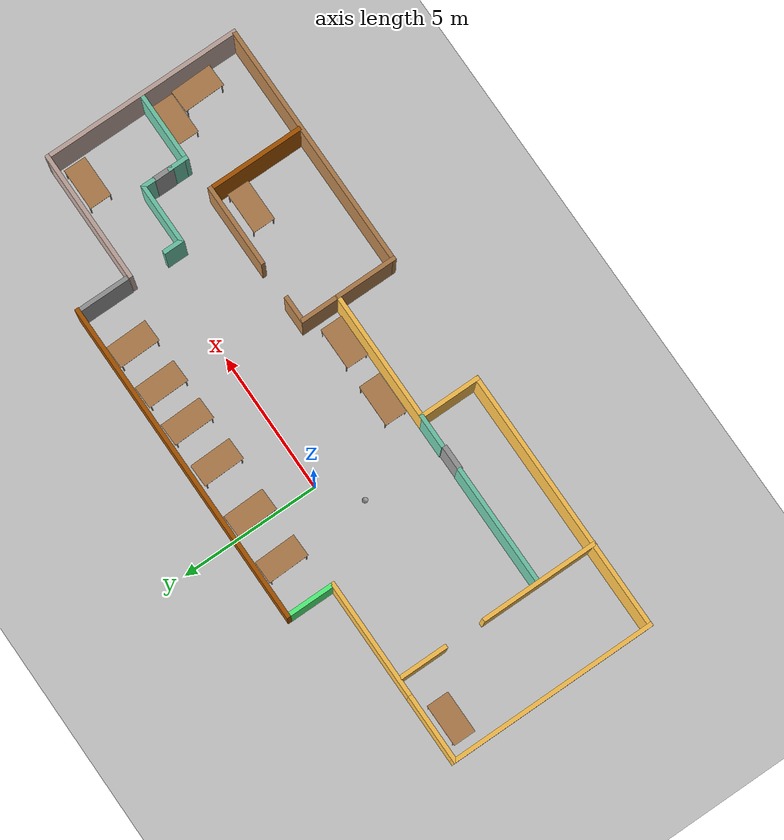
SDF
<sdf version="1.6">
 <world name="default">
  <plugin name="welcome_message" filename="libwelcome_message.so"/>
  <light name="sun" type="directional">
   <pose>0 0 10 0 -0 0</pose>
   <diffuse>0.8 0.8 0.8 1</diffuse>
   <specular>0.1 0.1 0.1 1</specular>
   <attenuation>
    <range>1000</range>
    <constant>0.9</constant>
    <linear>0.01</linear>
    <quadratic>0.001</quadratic>
   </attenuation>
   <direction>-0.5 0.5 -1</direction>
  </light>
  <model name="ground_plane">
   <static>1</static>
   <link name="link">
    <collision name="collision">
     <geometry><plane><normal>0 0 1</normal><size>100 100</size></plane></geometry>
     <surface><friction><ode><mu>100</mu><mu2>50</mu2></ode></friction></surface>
    </collision>
    <visual name="visual">
     <cast_shadows>0</cast_shadows>
     <geometry><plane><normal>0 0 1</normal><size>100 100</size></plane></geometry>
     <material>
      <script><uri>file://media/materials/scripts/gazebo.material</uri><name>Gazebo/Grey</name></script>
     </material>
    </visual>
   </link>
  </model>
  <gravity>0 0 -9.8</gravity>
  <magnetic_field>6e-06 2.3e-05 -4.2e-05</magnetic_field>
  <atmosphere type="adiabatic"/>
  <physics name="default_physics" default="0" type="ode">
   <max_step_size>0.001</max_step_size>
   <real_time_factor>1</real_time_factor>
   <real_time_update_rate>1000</real_time_update_rate>
  </physics>
  <scene><ambient>0.4 0.4 0.4 1</ambient><background>0.7 0.7 0.7 1</background><shadows>1</shadows></scene>
  <spherical_coordinates>
   <surface_model>EARTH_WGS84</surface_model>
   <latitude_deg>0</latitude_deg>
   <longitude_deg>0</longitude_deg>
   <elevation>0</elevation>
   <heading_deg>0</heading_deg>
  </spherical_coordinates>
  <model name="Building">
   <model name="Udacity_Office">
    <link name="Door_0">
     <pose>-3.67047 -1.60909 0 0 -0 0</pose>
     <visual name="Door_0_Visual">
      <pose>0 0 1.25 0 -0 0</pose>
      <geometry><box><size>0.9 0.17 2.5</size></box></geometry>
      <material>
       <script><uri>file://media/materials/scripts/gazebo.material</uri><name>Gazebo/Grey</name></script>
       <shader type="pixel"/>
       <ambient>0.3 0.3 0.3 1</ambient>
       <diffuse>0.7 0.7 0.7 1</diffuse>
       <specular>0.01 0.01 0.01 1</specular>
       <emissive>0 0 0 1</emissive>
      </material>
     </visual>
     <collision name="Door_0_Collision">
      <pose>0 0 1.25 0 -0 0</pose>
      <geometry><box><size>0.9 0.17 2.5</size></box></geometry>
      <surface>
       <friction>
        <ode><mu>1</mu><mu2>1</mu2><fdir1>0 0 0</fdir1><slip1>0</slip1><slip2>0</slip2></ode>
        <torsional>
         <coefficient>1</coefficient>
         <patch_radius>0</patch_radius>
         <surface_radius>0</surface_radius>
         <use_patch_radius>1</use_patch_radius>
         <ode><slip>0</slip></ode>
        </torsional>
       </friction>
       <bounce><restitution_coefficient>0</restitution_coefficient><threshold>1e+06</threshold></bounce>
       <contact>
        <collide_without_contact>0</collide_without_contact>
        <collide_without_contact_bitmask>1</collide_without_contact_bitmask>
        <collide_bitmask>1</collide_bitmask>
        <ode>
         <soft_cfm>0</soft_cfm>
         <soft_erp>0.2</soft_erp>
         <kp>1e+13</kp>
         <kd>1</kd>
         <max_vel>0.01</max_vel>
         <min_depth>0</min_depth>
        </ode>
        <bullet>
         <split_impulse>1</split_impulse>
         <split_impulse_penetration_threshold>-0.01</split_impulse_penetration_threshold>
         <soft_cfm>0</soft_cfm>
         <soft_erp>0.2</soft_erp>
         <kp>1e+13</kp>
         <kd>1</kd>
        </bullet>
       </contact>
      </surface>
     </collision>
    </link>
    <link name="Door_1">
     <pose>8.90051 0.744202 0 0 0 -1.5708</pose>
     <visual name="Door_1_Visual">
      <pose>0 0 1.25 0 -0 0</pose>
      <geometry><box><size>0.7 0.17 2.5</size></box></geometry>
      <material>
       <script><uri>file://media/materials/scripts/gazebo.material</uri><name>Gazebo/Grey</name></script>
       <shader type="pixel"/>
       <ambient>0.3 0.3 0.3 1</ambient>
       <diffuse>0.7 0.7 0.7 1</diffuse>
       <specular>0.01 0.01 0.01 1</specular>
       <emissive>0 0 0 1</emissive>
      </material>
     </visual>
     <collision name="Door_1_Collision">
      <pose>0 0 1.25 0 -0 0</pose>
      <geometry><box><size>0.7 0.17 2.5</size></box></geometry>
      <surface>
       <friction>
        <ode><mu>1</mu><mu2>1</mu2><fdir1>0 0 0</fdir1><slip1>0</slip1><slip2>0</slip2></ode>
        <torsional>
         <coefficient>1</coefficient>
         <patch_radius>0</patch_radius>
         <surface_radius>0</surface_radius>
         <use_patch_radius>1</use_patch_radius>
         <ode><slip>0</slip></ode>
        </torsional>
       </friction>
       <bounce><restitution_coefficient>0</restitution_coefficient><threshold>1e+06</threshold></bounce>
       <contact>
        <collide_without_contact>0</collide_without_contact>
        <collide_without_contact_bitmask>1</collide_without_contact_bitmask>
        <collide_bitmask>1</collide_bitmask>
        <ode>
         <soft_cfm>0</soft_cfm>
         <soft_erp>0.2</soft_erp>
         <kp>1e+13</kp>
         <kd>1</kd>
         <max_vel>0.01</max_vel>
         <min_depth>0</min_depth>
        </ode>
        <bullet>
         <split_impulse>1</split_impulse>
         <split_impulse_penetration_threshold>-0.01</split_impulse_penetration_threshold>
         <soft_cfm>0</soft_cfm>
         <soft_erp>0.2</soft_erp>
         <kp>1e+13</kp>
         <kd>1</kd>
        </bullet>
       </contact>
      </surface>
     </collision>
    </link>
    <link name="Wall_0">
     <pose>-6.85 3.68078 0 0 -0 0</pose>
     <visual name="Wall_0_Visual">
      <pose>0 0 1.25 0 -0 0</pose>
      <geometry><box><size>4.25 0.15 2.5</size></box></geometry>
      <material>
       <script><uri>file://media/materials/scripts/gazebo.material</uri><name>Gazebo/Grey</name></script>
       <ambient>1 0.764706 0.305882 1</ambient>
       <shader type="pixel"/>
       <diffuse>0.7 0.7 0.7 1</diffuse>
       <specular>0.01 0.01 0.01 1</specular>
       <emissive>0 0 0 1</emissive>
      </material>
      <meta><layer>0</layer></meta>
     </visual>
     <collision name="Wall_0_Collision">
      <pose>0 0 1.25 0 -0 0</pose>
      <geometry><box><size>4.25 0.15 2.5</size></box></geometry>
      <surface>
       <friction>
        <ode><mu>1</mu><mu2>1</mu2><fdir1>0 0 0</fdir1><slip1>0</slip1><slip2>0</slip2></ode>
        <torsional>
         <coefficient>1</coefficient>
         <patch_radius>0</patch_radius>
         <surface_radius>0</surface_radius>
         <use_patch_radius>1</use_patch_radius>
         <ode><slip>0</slip></ode>
        </torsional>
       </friction>
       <bounce><restitution_coefficient>0</restitution_coefficient><threshold>1e+06</threshold></bounce>
       <contact>
        <collide_without_contact>0</collide_without_contact>
        <collide_without_contact_bitmask>1</collide_without_contact_bitmask>
        <collide_bitmask>1</collide_bitmask>
        <ode>
         <soft_cfm>0</soft_cfm>
         <soft_erp>0.2</soft_erp>
         <kp>1e+13</kp>
         <kd>1</kd>
         <max_vel>0.01</max_vel>
         <min_depth>0</min_depth>
        </ode>
        <bullet>
         <split_impulse>1</split_impulse>
         <split_impulse_penetration_threshold>-0.01</split_impulse_penetration_threshold>
         <soft_cfm>0</soft_cfm>
         <soft_erp>0.2</soft_erp>
         <kp>1e+13</kp>
         <kd>1</kd>
        </bullet>
       </contact>
      </surface>
     </collision>
    </link>
    <link name="Wall_1">
     <pose>-4.79999 4.59263 0 0 0 -1.5708</pose>
     <visual name="Wall_1_Visual">
      <pose>0 0 1.25 0 -0 0</pose>
      <geometry><box><size>1.75 0.15 2.5</size></box></geometry>
      <material>
       <script><uri>file://media/materials/scripts/gazebo.material</uri><name>Gazebo/Grey</name></script>
       <ambient>0.333333 1 0.498039 1</ambient>
       <shader type="pixel"/>
       <diffuse>0.7 0.7 0.7 1</diffuse>
       <specular>0.01 0.01 0.01 1</specular>
       <emissive>0 0 0 1</emissive>
      </material>
      <meta><layer>0</layer></meta>
     </visual>
     <collision name="Wall_1_Collision">
      <pose>0 0 1.25 0 -0 0</pose>
      <geometry><box><size>1.75 0.15 2.5</size></box></geometry>
      <surface>
       <friction>
        <ode><mu>1</mu><mu2>1</mu2><fdir1>0 0 0</fdir1><slip1>0</slip1><slip2>0</slip2></ode>
        <torsional>
         <coefficient>1</coefficient>
         <patch_radius>0</patch_radius>
         <surface_radius>0</surface_radius>
         <use_patch_radius>1</use_patch_radius>
         <ode><slip>0</slip></ode>
        </torsional>
       </friction>
       <bounce><restitution_coefficient>0</restitution_coefficient><threshold>1e+06</threshold></bounce>
       <contact>
        <collide_without_contact>0</collide_without_contact>
        <collide_without_contact_bitmask>1</collide_without_contact_bitmask>
        <collide_bitmask>1</collide_bitmask>
        <ode>
         <soft_cfm>0</soft_cfm>
         <soft_erp>0.2</soft_erp>
         <kp>1e+13</kp>
         <kd>1</kd>
         <max_vel>0.01</max_vel>
         <min_depth>0</min_depth>
        </ode>
        <bullet>
         <split_impulse>1</split_impulse>
         <split_impulse_penetration_threshold>-0.01</split_impulse_penetration_threshold>
         <soft_cfm>0</soft_cfm>
         <soft_erp>0.2</soft_erp>
         <kp>1e+13</kp>
         <kd>1</kd>
        </bullet>
       </contact>
      </surface>
     </collision>
    </link>
    <link name="Wall_10">
     <pose>-6.725 -3.66922 0 0 -0 3.14159</pose>
     <visual name="Wall_10_Visual">
      <pose>0 0 1.25 0 -0 0</pose>
      <geometry><box><size>9.5 0.15 2.5</size></box></geometry>
      <material>
       <script><uri>file://media/materials/scripts/gazebo.material</uri><name>Gazebo/Grey</name></script>
       <ambient>1 0.764706 0.305882 1</ambient>
       <shader type="pixel"/>
       <diffuse>0.7 0.7 0.7 1</diffuse>
       <specular>0.01 0.01 0.01 1</specular>
       <emissive>0 0 0 1</emissive>
      </material>
      <meta><layer>0</layer></meta>
     </visual>
     <collision name="Wall_10_Collision">
      <pose>0 0 1.25 0 -0 0</pose>
      <geometry><box><size>9.5 0.15 2.5</size></box></geometry>
      <surface>
       <friction>
        <ode><mu>1</mu><mu2>1</mu2><fdir1>0 0 0</fdir1><slip1>0</slip1><slip2>0</slip2></ode>
        <torsional>
         <coefficient>1</coefficient>
         <patch_radius>0</patch_radius>
         <surface_radius>0</surface_radius>
         <use_patch_radius>1</use_patch_radius>
         <ode><slip>0</slip></ode>
        </torsional>
       </friction>
       <bounce><restitution_coefficient>0</restitution_coefficient><threshold>1e+06</threshold></bounce>
       <contact>
        <collide_without_contact>0</collide_without_contact>
        <collide_without_contact_bitmask>1</collide_without_contact_bitmask>
        <collide_bitmask>1</collide_bitmask>
        <ode>
         <soft_cfm>0</soft_cfm>
         <soft_erp>0.2</soft_erp>
         <kp>1e+13</kp>
         <kd>1</kd>
         <max_vel>0.01</max_vel>
         <min_depth>0</min_depth>
        </ode>
        <bullet>
         <split_impulse>1</split_impulse>
         <split_impulse_penetration_threshold>-0.01</split_impulse_penetration_threshold>
         <soft_cfm>0</soft_cfm>
         <soft_erp>0.2</soft_erp>
         <kp>1e+13</kp>
         <kd>1</kd>
        </bullet>
       </contact>
      </surface>
     </collision>
    </link>
    <link name="Wall_11">
     <pose>-11.4 0.005784 0 0 -0 1.5708</pose>
     <visual name="Wall_11_Visual">
      <pose>0 0 1.25 0 -0 0</pose>
      <geometry><box><size>7.5 0.15 2.5</size></box></geometry>
      <material>
       <script><uri>file://media/materials/scripts/gazebo.material</uri><name>Gazebo/Grey</name></script>
       <ambient>1 0.764706 0.305882 1</ambient>
       <shader type="pixel"/>
       <diffuse>0.7 0.7 0.7 1</diffuse>
       <specular>0.01 0.01 0.01 1</specular>
       <emissive>0 0 0 1</emissive>
      </material>
      <meta><layer>0</layer></meta>
     </visual>
     <collision name="Wall_11_Collision">
      <pose>0 0 1.25 0 -0 0</pose>
      <geometry><box><size>7.5 0.15 2.5</size></box></geometry>
      <surface>
       <friction>
        <ode><mu>1</mu><mu2>1</mu2><fdir1>0 0 0</fdir1><slip1>0</slip1><slip2>0</slip2></ode>
        <torsional>
         <coefficient>1</coefficient>
         <patch_radius>0</patch_radius>
         <surface_radius>0</surface_radius>
         <use_patch_radius>1</use_patch_radius>
         <ode><slip>0</slip></ode>
        </torsional>
       </friction>
       <bounce><restitution_coefficient>0</restitution_coefficient><threshold>1e+06</threshold></bounce>
       <contact>
        <collide_without_contact>0</collide_without_contact>
        <collide_without_contact_bitmask>1</collide_without_contact_bitmask>
        <collide_bitmask>1</collide_bitmask>
        <ode>
         <soft_cfm>0</soft_cfm>
         <soft_erp>0.2</soft_erp>
         <kp>1e+13</kp>
         <kd>1</kd>
         <max_vel>0.01</max_vel>
         <min_depth>0</min_depth>
        </ode>
        <bullet>
         <split_impulse>1</split_impulse>
         <split_impulse_penetration_threshold>-0.01</split_impulse_penetration_threshold>
         <soft_cfm>0</soft_cfm>
         <soft_erp>0.2</soft_erp>
         <kp>1e+13</kp>
         <kd>1</kd>
        </bullet>
       </contact>
      </surface>
     </collision>
    </link>
    <link name="Wall_12">
     <pose>-10.15 3.68078 0 0 -0 0</pose>
     <visual name="Wall_12_Visual">
      <pose>0 0 1.25 0 -0 0</pose>
      <geometry><box><size>2.65 0.15 2.5</size></box></geometry>
      <material>
       <script><uri>file://media/materials/scripts/gazebo.material</uri><name>Gazebo/Grey</name></script>
       <ambient>1 0.764706 0.305882 1</ambient>
       <shader type="pixel"/>
       <diffuse>0.7 0.7 0.7 1</diffuse>
       <specular>0.01 0.01 0.01 1</specular>
       <emissive>0 0 0 1</emissive>
      </material>
      <meta><layer>0</layer></meta>
     </visual>
     <collision name="Wall_12_Collision">
      <pose>0 0 1.25 0 -0 0</pose>
      <geometry><box><size>2.65 0.15 2.5</size></box></geometry>
      <surface>
       <friction>
        <ode><mu>1</mu><mu2>1</mu2><fdir1>0 0 0</fdir1><slip1>0</slip1><slip2>0</slip2></ode>
        <torsional>
         <coefficient>1</coefficient>
         <patch_radius>0</patch_radius>
         <surface_radius>0</surface_radius>
         <use_patch_radius>1</use_patch_radius>
         <ode><slip>0</slip></ode>
        </torsional>
       </friction>
       <bounce><restitution_coefficient>0</restitution_coefficient><threshold>1e+06</threshold></bounce>
       <contact>
        <collide_without_contact>0</collide_without_contact>
        <collide_without_contact_bitmask>1</collide_without_contact_bitmask>
        <collide_bitmask>1</collide_bitmask>
        <ode>
         <soft_cfm>0</soft_cfm>
         <soft_erp>0.2</soft_erp>
         <kp>1e+13</kp>
         <kd>1</kd>
         <max_vel>0.01</max_vel>
         <min_depth>0</min_depth>
        </ode>
        <bullet>
         <split_impulse>1</split_impulse>
         <split_impulse_penetration_threshold>-0.01</split_impulse_penetration_threshold>
         <soft_cfm>0</soft_cfm>
         <soft_erp>0.2</soft_erp>
         <kp>1e+13</kp>
         <kd>1</kd>
        </bullet>
       </contact>
      </surface>
     </collision>
    </link>
    <link name="Wall_19">
     <pose>2.55 -0.894216 0 0 -0 1.5708</pose>
     <visual name="Wall_19_Visual">
      <pose>0 0 1.25 0 -0 0</pose>
      <geometry><box><size>1.5 0.15 2.5</size></box></geometry>
      <material>
       <script><uri>file://media/materials/scripts/gazebo.material</uri><name>Gazebo/Wood</name></script>
       <ambient>1 0.764706 0.305882 1</ambient>
       <shader type="pixel"/>
       <diffuse>1 1 1 1</diffuse>
       <specular>0.2 0.2 0.2 1</specular>
       <emissive>0 0 0 1</emissive>
      </material>
      <meta><layer>0</layer></meta>
     </visual>
     <collision name="Wall_19_Collision">
      <pose>0 0 1.25 0 -0 0</pose>
      <geometry><box><size>1.5 0.15 2.5</size></box></geometry>
      <surface>
       <friction>
        <ode><mu>1</mu><mu2>1</mu2><fdir1>0 0 0</fdir1><slip1>0</slip1><slip2>0</slip2></ode>
        <torsional>
         <coefficient>1</coefficient>
         <patch_radius>0</patch_radius>
         <surface_radius>0</surface_radius>
         <use_patch_radius>1</use_patch_radius>
         <ode><slip>0</slip></ode>
        </torsional>
       </friction>
       <bounce><restitution_coefficient>0</restitution_coefficient><threshold>1e+06</threshold></bounce>
       <contact>
        <collide_without_contact>0</collide_without_contact>
        <collide_without_contact_bitmask>1</collide_without_contact_bitmask>
        <collide_bitmask>1</collide_bitmask>
        <ode>
         <soft_cfm>0</soft_cfm>
         <soft_erp>0.2</soft_erp>
         <kp>1e+13</kp>
         <kd>1</kd>
         <max_vel>0.01</max_vel>
         <min_depth>0</min_depth>
        </ode>
        <bullet>
         <split_impulse>1</split_impulse>
         <split_impulse_penetration_threshold>-0.01</split_impulse_penetration_threshold>
         <soft_cfm>0</soft_cfm>
         <soft_erp>0.2</soft_erp>
         <kp>1e+13</kp>
         <kd>1</kd>
        </bullet>
       </contact>
      </surface>
     </collision>
    </link>
    <link name="Wall_2">
     <pose>1 5.39525 0 0 -0 0</pose>
     <visual name="Wall_2_Visual">
      <pose>0 0 1.25 0 -0 0</pose>
      <geometry><box><size>11.75 0.15 2.5</size></box></geometry>
      <material>
       <script><uri>file://media/materials/scripts/gazebo.material</uri><name>Gazebo/Grey</name></script>
       <ambient>0.666667 0.333333 0 1</ambient>
       <shader type="pixel"/>
       <diffuse>0.7 0.7 0.7 1</diffuse>
       <specular>0.01 0.01 0.01 1</specular>
       <emissive>0 0 0 1</emissive>
      </material>
      <meta><layer>0</layer></meta>
     </visual>
     <collision name="Wall_2_Collision">
      <pose>0 0 1.25 0 -0 0</pose>
      <geometry><box><size>11.75 0.15 2.5</size></box></geometry>
      <surface>
       <friction>
        <ode><mu>1</mu><mu2>1</mu2><fdir1>0 0 0</fdir1><slip1>0</slip1><slip2>0</slip2></ode>
        <torsional>
         <coefficient>1</coefficient>
         <patch_radius>0</patch_radius>
         <surface_radius>0</surface_radius>
         <use_patch_radius>1</use_patch_radius>
         <ode><slip>0</slip></ode>
        </torsional>
       </friction>
       <bounce><restitution_coefficient>0</restitution_coefficient><threshold>1e+06</threshold></bounce>
       <contact>
        <collide_without_contact>0</collide_without_contact>
        <collide_without_contact_bitmask>1</collide_without_contact_bitmask>
        <collide_bitmask>1</collide_bitmask>
        <ode>
         <soft_cfm>0</soft_cfm>
         <soft_erp>0.2</soft_erp>
         <kp>1e+13</kp>
         <kd>1</kd>
         <max_vel>0.01</max_vel>
         <min_depth>0</min_depth>
        </ode>
        <bullet>
         <split_impulse>1</split_impulse>
         <split_impulse_penetration_threshold>-0.01</split_impulse_penetration_threshold>
         <soft_cfm>0</soft_cfm>
         <soft_erp>0.2</soft_erp>
         <kp>1e+13</kp>
         <kd>1</kd>
        </bullet>
       </contact>
      </surface>
     </collision>
    </link>
    <link name="Wall_24">
     <pose>7.65 -1.89422 0 0 0 -1.5708</pose>
     <visual name="Wall_24_Visual">
      <pose>0 0 1.25 0 -0 0</pose>
      <geometry><box><size>3.5 0.15 2.5</size></box></geometry>
      <material>
       <script><uri>file://media/materials/scripts/gazebo.material</uri><name>Gazebo/Grey</name></script>
       <ambient>0.666667 0.333333 0 1</ambient>
       <shader type="pixel"/>
       <diffuse>0.7 0.7 0.7 1</diffuse>
       <specular>0.01 0.01 0.01 1</specular>
       <emissive>0 0 0 1</emissive>
      </material>
      <meta><layer>0</layer></meta>
     </visual>
     <collision name="Wall_24_Collision">
      <pose>0 0 1.25 0 -0 0</pose>
      <geometry><box><size>3.5 0.15 2.5</size></box></geometry>
      <surface>
       <friction>
        <ode><mu>1</mu><mu2>1</mu2><fdir1>0 0 0</fdir1><slip1>0</slip1><slip2>0</slip2></ode>
        <torsional>
         <coefficient>1</coefficient>
         <patch_radius>0</patch_radius>
         <surface_radius>0</surface_radius>
         <use_patch_radius>1</use_patch_radius>
         <ode><slip>0</slip></ode>
        </torsional>
       </friction>
       <bounce><restitution_coefficient>0</restitution_coefficient><threshold>1e+06</threshold></bounce>
       <contact>
        <collide_without_contact>0</collide_without_contact>
        <collide_without_contact_bitmask>1</collide_without_contact_bitmask>
        <collide_bitmask>1</collide_bitmask>
        <ode>
         <soft_cfm>0</soft_cfm>
         <soft_erp>0.2</soft_erp>
         <kp>1e+13</kp>
         <kd>1</kd>
         <max_vel>0.01</max_vel>
         <min_depth>0</min_depth>
        </ode>
        <bullet>
         <split_impulse>1</split_impulse>
         <split_impulse_penetration_threshold>-0.01</split_impulse_penetration_threshold>
         <soft_cfm>0</soft_cfm>
         <soft_erp>0.2</soft_erp>
         <kp>1e+13</kp>
         <kd>1</kd>
        </bullet>
       </contact>
      </surface>
     </collision>
    </link>
    <link name="Wall_26">
     <pose>6.8 1.78078 0 0 0 -1.5708</pose>
     <visual name="Wall_26_Visual">
      <pose>0 0 1.25 0 -0 0</pose>
      <geometry><box><size>0.75 0.15 2.5</size></box></geometry>
      <material>
       <script><uri>file://media/materials/scripts/gazebo.material</uri><name>Gazebo/Grey</name></script>
       <ambient>0.435294 0.796078 0.67451 1</ambient>
       <shader type="pixel"/>
       <diffuse>0.7 0.7 0.7 1</diffuse>
       <specular>0.01 0.01 0.01 1</specular>
       <emissive>0 0 0 1</emissive>
      </material>
      <meta><layer>0</layer></meta>
     </visual>
     <collision name="Wall_26_Collision">
      <pose>0 0 1.25 0 -0 0</pose>
      <geometry><box><size>0.75 0.15 2.5</size></box></geometry>
      <surface>
       <friction>
        <ode><mu>1</mu><mu2>1</mu2><fdir1>0 0 0</fdir1><slip1>0</slip1><slip2>0</slip2></ode>
        <torsional>
         <coefficient>1</coefficient>
         <patch_radius>0</patch_radius>
         <surface_radius>0</surface_radius>
         <use_patch_radius>1</use_patch_radius>
         <ode><slip>0</slip></ode>
        </torsional>
       </friction>
       <bounce><restitution_coefficient>0</restitution_coefficient><threshold>1e+06</threshold></bounce>
       <contact>
        <collide_without_contact>0</collide_without_contact>
        <collide_without_contact_bitmask>1</collide_without_contact_bitmask>
        <collide_bitmask>1</collide_bitmask>
        <ode>
         <soft_cfm>0</soft_cfm>
         <soft_erp>0.2</soft_erp>
         <kp>1e+13</kp>
         <kd>1</kd>
         <max_vel>0.01</max_vel>
         <min_depth>0</min_depth>
        </ode>
        <bullet>
         <split_impulse>1</split_impulse>
         <split_impulse_penetration_threshold>-0.01</split_impulse_penetration_threshold>
         <soft_cfm>0</soft_cfm>
         <soft_erp>0.2</soft_erp>
         <kp>1e+13</kp>
         <kd>1</kd>
        </bullet>
       </contact>
      </surface>
     </collision>
    </link>
    <link name="Wall_27">
     <pose>7.85 1.48078 0 0 -0 0</pose>
     <visual name="Wall_27_Visual">
      <pose>0 0 1.25 0 -0 0</pose>
      <geometry><box><size>2.25 0.15 2.5</size></box></geometry>
      <material>
       <script><uri>file://media/materials/scripts/gazebo.material</uri><name>Gazebo/Grey</name></script>
       <ambient>0.435294 0.796078 0.67451 1</ambient>
       <shader type="pixel"/>
       <diffuse>0.7 0.7 0.7 1</diffuse>
       <specular>0.01 0.01 0.01 1</specular>
       <emissive>0 0 0 1</emissive>
      </material>
      <meta><layer>0</layer></meta>
     </visual>
     <collision name="Wall_27_Collision">
      <pose>0 0 1.25 0 -0 0</pose>
      <geometry><box><size>2.25 0.15 2.5</size></box></geometry>
      <surface>
       <friction>
        <ode><mu>1</mu><mu2>1</mu2><fdir1>0 0 0</fdir1><slip1>0</slip1><slip2>0</slip2></ode>
        <torsional>
         <coefficient>1</coefficient>
         <patch_radius>0</patch_radius>
         <surface_radius>0</surface_radius>
         <use_patch_radius>1</use_patch_radius>
         <ode><slip>0</slip></ode>
        </torsional>
       </friction>
       <bounce><restitution_coefficient>0</restitution_coefficient><threshold>1e+06</threshold></bounce>
       <contact>
        <collide_without_contact>0</collide_without_contact>
        <collide_without_contact_bitmask>1</collide_without_contact_bitmask>
        <collide_bitmask>1</collide_bitmask>
        <ode>
         <soft_cfm>0</soft_cfm>
         <soft_erp>0.2</soft_erp>
         <kp>1e+13</kp>
         <kd>1</kd>
         <max_vel>0.01</max_vel>
         <min_depth>0</min_depth>
        </ode>
        <bullet>
         <split_impulse>1</split_impulse>
         <split_impulse_penetration_threshold>-0.01</split_impulse_penetration_threshold>
         <soft_cfm>0</soft_cfm>
         <soft_erp>0.2</soft_erp>
         <kp>1e+13</kp>
         <kd>1</kd>
        </bullet>
       </contact>
      </surface>
     </collision>
    </link>
    <link name="Wall_29">
     <pose>10.075 -0.119216 0 0 -0 0</pose>
     <visual name="Wall_29_Visual">
      <pose>0 0 1.25 0 -0 0</pose>
      <geometry><box><size>2.5 0.15 2.5</size></box></geometry>
      <material>
       <script><uri>file://media/materials/scripts/gazebo.material</uri><name>Gazebo/Grey</name></script>
       <ambient>0.435294 0.796078 0.67451 1</ambient>
       <shader type="pixel"/>
       <diffuse>0.7 0.7 0.7 1</diffuse>
       <specular>0.01 0.01 0.01 1</specular>
       <emissive>0 0 0 1</emissive>
      </material>
      <meta><layer>0</layer></meta>
     </visual>
     <collision name="Wall_29_Collision">
      <pose>0 0 1.25 0 -0 0</pose>
      <geometry><box><size>2.5 0.15 2.5</size></box></geometry>
      <surface>
       <friction>
        <ode><mu>1</mu><mu2>1</mu2><fdir1>0 0 0</fdir1><slip1>0</slip1><slip2>0</slip2></ode>
        <torsional>
         <coefficient>1</coefficient>
         <patch_radius>0</patch_radius>
         <surface_radius>0</surface_radius>
         <use_patch_radius>1</use_patch_radius>
         <ode><slip>0</slip></ode>
        </torsional>
       </friction>
       <bounce><restitution_coefficient>0</restitution_coefficient><threshold>1e+06</threshold></bounce>
       <contact>
        <collide_without_contact>0</collide_without_contact>
        <collide_without_contact_bitmask>1</collide_without_contact_bitmask>
        <collide_bitmask>1</collide_bitmask>
        <ode>
         <soft_cfm>0</soft_cfm>
         <soft_erp>0.2</soft_erp>
         <kp>1e+13</kp>
         <kd>1</kd>
         <max_vel>0.01</max_vel>
         <min_depth>0</min_depth>
        </ode>
        <bullet>
         <split_impulse>1</split_impulse>
         <split_impulse_penetration_threshold>-0.01</split_impulse_penetration_threshold>
         <soft_cfm>0</soft_cfm>
         <soft_erp>0.2</soft_erp>
         <kp>1e+13</kp>
         <kd>1</kd>
        </bullet>
       </contact>
      </surface>
     </collision>
    </link>
    <link name="Wall_3">
     <pose>6.78568 4.42312 0 0 -0 1.5708</pose>
     <inertial>
      <mass>1</mass>
      <inertia><ixx>1</ixx><ixy>0</ixy><ixz>0</ixz><iyy>1</iyy><iyz>0</iyz><izz>1</izz></inertia>
     </inertial>
     <visual name="Wall_3_Visual">
      <pose>0 0 1.25 0 -0 0</pose>
      <geometry><box><size>1.8 0.15 2.5</size></box></geometry>
      <material>
       <script><uri>file://media/materials/scripts/gazebo.material</uri><name>Gazebo/Grey</name></script>
       <ambient>1 1 1 1</ambient>
       <shader type="pixel"><normal_map>__default__</normal_map></shader>
       <diffuse>0.7 0.7 0.7 1</diffuse>
       <specular>0.01 0.01 0.01 1</specular>
       <emissive>0 0 0 1</emissive>
      </material>
      <meta><layer>0</layer></meta>
     </visual>
     <collision name="Wall_3_Collision">
      <pose>0 0 1.25 0 -0 0</pose>
      <geometry><box><size>1.5 0.15 2.5</size></box></geometry>
      <surface>
       <friction>
        <ode><mu>1</mu><mu2>1</mu2><fdir1>0 0 0</fdir1><slip1>0</slip1><slip2>0</slip2></ode>
        <torsional>
         <coefficient>1</coefficient>
         <patch_radius>0</patch_radius>
         <surface_radius>0</surface_radius>
         <use_patch_radius>1</use_patch_radius>
         <ode><slip>0</slip></ode>
        </torsional>
       </friction>
       <bounce><restitution_coefficient>0</restitution_coefficient><threshold>1e+06</threshold></bounce>
       <contact>
        <collide_without_contact>0</collide_without_contact>
        <collide_without_contact_bitmask>1</collide_without_contact_bitmask>
        <collide_bitmask>1</collide_bitmask>
        <ode>
         <soft_cfm>0</soft_cfm>
         <soft_erp>0.2</soft_erp>
         <kp>1e+13</kp>
         <kd>1</kd>
         <max_vel>0.01</max_vel>
         <min_depth>0</min_depth>
        </ode>
        <bullet>
         <split_impulse>1</split_impulse>
         <split_impulse_penetration_threshold>-0.01</split_impulse_penetration_threshold>
         <soft_cfm>0</soft_cfm>
         <soft_erp>0.2</soft_erp>
         <kp>1e+13</kp>
         <kd>1</kd>
        </bullet>
       </contact>
      </surface>
     </collision>
    </link>
    <link name="Wall_38">
     <pose>-2.6 -1.56922 0 0 -0 3.14159</pose>
     <visual name="Wall_38_Visual">
      <pose>0 0 1.25 0 -0 0</pose>
      <geometry><box><size>1.25 0.15 2.5</size></box></geometry>
      <material>
       <script><uri>file://media/materials/scripts/gazebo.material</uri><name>Gazebo/Grey</name></script>
       <ambient>0.435294 0.796078 0.67451 1</ambient>
       <shader type="pixel"/>
       <diffuse>0.7 0.7 0.7 1</diffuse>
       <specular>0.01 0.01 0.01 1</specular>
       <emissive>0 0 0 1</emissive>
      </material>
      <meta><layer>0</layer></meta>
     </visual>
     <collision name="Wall_38_Collision">
      <pose>0 0 1.25 0 -0 0</pose>
      <geometry><box><size>1.25 0.15 2.5</size></box></geometry>
      <surface>
       <friction>
        <ode><mu>1</mu><mu2>1</mu2><fdir1>0 0 0</fdir1><slip1>0</slip1><slip2>0</slip2></ode>
        <torsional>
         <coefficient>1</coefficient>
         <patch_radius>0</patch_radius>
         <surface_radius>0</surface_radius>
         <use_patch_radius>1</use_patch_radius>
         <ode><slip>0</slip></ode>
        </torsional>
       </friction>
       <bounce><restitution_coefficient>0</restitution_coefficient><threshold>1e+06</threshold></bounce>
       <contact>
        <collide_without_contact>0</collide_without_contact>
        <collide_without_contact_bitmask>1</collide_without_contact_bitmask>
        <collide_bitmask>1</collide_bitmask>
        <ode>
         <soft_cfm>0</soft_cfm>
         <soft_erp>0.2</soft_erp>
         <kp>1e+13</kp>
         <kd>1</kd>
         <max_vel>0.01</max_vel>
         <min_depth>0</min_depth>
        </ode>
        <bullet>
         <split_impulse>1</split_impulse>
         <split_impulse_penetration_threshold>-0.01</split_impulse_penetration_threshold>
         <soft_cfm>0</soft_cfm>
         <soft_erp>0.2</soft_erp>
         <kp>1e+13</kp>
         <kd>1</kd>
        </bullet>
       </contact>
      </surface>
     </collision>
    </link>
    <link name="Wall_4">
     <pose>9.1 3.43078 0 0 -0 0</pose>
     <visual name="Wall_4_Visual">
      <pose>0 0 1.25 0 -0 0</pose>
      <geometry><box><size>4.75 0.15 2.5</size></box></geometry>
      <material>
       <script><uri>file://media/materials/scripts/gazebo.material</uri><name>Gazebo/Grey</name></script>
       <ambient>0.760784 0.662745 0.627451 1</ambient>
       <shader type="pixel"/>
       <diffuse>0.7 0.7 0.7 1</diffuse>
       <specular>0.01 0.01 0.01 1</specular>
       <emissive>0 0 0 1</emissive>
      </material>
      <meta><layer>0</layer></meta>
     </visual>
     <collision name="Wall_4_Collision">
      <pose>0 0 1.25 0 -0 0</pose>
      <geometry><box><size>4.75 0.15 2.5</size></box></geometry>
      <surface>
       <friction>
        <ode><mu>1</mu><mu2>1</mu2><fdir1>0 0 0</fdir1><slip1>0</slip1><slip2>0</slip2></ode>
        <torsional>
         <coefficient>1</coefficient>
         <patch_radius>0</patch_radius>
         <surface_radius>0</surface_radius>
         <use_patch_radius>1</use_patch_radius>
         <ode><slip>0</slip></ode>
        </torsional>
       </friction>
       <bounce><restitution_coefficient>0</restitution_coefficient><threshold>1e+06</threshold></bounce>
       <contact>
        <collide_without_contact>0</collide_without_contact>
        <collide_without_contact_bitmask>1</collide_without_contact_bitmask>
        <collide_bitmask>1</collide_bitmask>
        <ode>
         <soft_cfm>0</soft_cfm>
         <soft_erp>0.2</soft_erp>
         <kp>1e+13</kp>
         <kd>1</kd>
         <max_vel>0.01</max_vel>
         <min_depth>0</min_depth>
        </ode>
        <bullet>
         <split_impulse>1</split_impulse>
         <split_impulse_penetration_threshold>-0.01</split_impulse_penetration_threshold>
         <soft_cfm>0</soft_cfm>
         <soft_erp>0.2</soft_erp>
         <kp>1e+13</kp>
         <kd>1</kd>
        </bullet>
       </contact>
      </surface>
     </collision>
    </link>
    <link name="Wall_40">
     <pose>-6.16297 -1.58897 0 0 -0 3.14159</pose>
     <visual name="Wall_40_Visual">
      <pose>0 0 1.25 0 -0 0</pose>
      <geometry><box><size>4.25 0.15 2.5</size></box></geometry>
      <material>
       <script><uri>file://media/materials/scripts/gazebo.material</uri><name>Gazebo/Grey</name></script>
       <ambient>0.435294 0.796078 0.67451 1</ambient>
       <shader type="pixel"/>
       <diffuse>0.7 0.7 0.7 1</diffuse>
       <specular>0.01 0.01 0.01 1</specular>
       <emissive>0 0 0 1</emissive>
      </material>
      <meta><layer>0</layer></meta>
     </visual>
     <collision name="Wall_40_Collision">
      <pose>0 0 1.25 0 -0 0</pose>
      <geometry><box><size>4.25 0.15 2.5</size></box></geometry>
      <surface>
       <friction>
        <ode><mu>1</mu><mu2>1</mu2><fdir1>0 0 0</fdir1><slip1>0</slip1><slip2>0</slip2></ode>
        <torsional>
         <coefficient>1</coefficient>
         <patch_radius>0</patch_radius>
         <surface_radius>0</surface_radius>
         <use_patch_radius>1</use_patch_radius>
         <ode><slip>0</slip></ode>
        </torsional>
       </friction>
       <bounce><restitution_coefficient>0</restitution_coefficient><threshold>1e+06</threshold></bounce>
       <contact>
        <collide_without_contact>0</collide_without_contact>
        <collide_without_contact_bitmask>1</collide_without_contact_bitmask>
        <collide_bitmask>1</collide_bitmask>
        <ode>
         <soft_cfm>0</soft_cfm>
         <soft_erp>0.2</soft_erp>
         <kp>1e+13</kp>
         <kd>1</kd>
         <max_vel>0.01</max_vel>
         <min_depth>0</min_depth>
        </ode>
        <bullet>
         <split_impulse>1</split_impulse>
         <split_impulse_penetration_threshold>-0.01</split_impulse_penetration_threshold>
         <soft_cfm>0</soft_cfm>
         <soft_erp>0.2</soft_erp>
         <kp>1e+13</kp>
         <kd>1</kd>
        </bullet>
       </contact>
      </surface>
     </collision>
    </link>
    <link name="Wall_43">
     <pose>2.975 -0.219216 0 0 -0 0</pose>
     <visual name="Wall_43_Visual">
      <pose>0 0 1.25 0 -0 0</pose>
      <geometry><box><size>1 0.15 2.5</size></box></geometry>
      <material>
       <script><uri>file://media/materials/scripts/gazebo.material</uri><name>Gazebo/Wood</name></script>
       <ambient>1 1 1 1</ambient>
       <shader type="pixel"/>
       <diffuse>1 1 1 1</diffuse>
       <specular>0.2 0.2 0.2 1</specular>
       <emissive>0 0 0 1</emissive>
      </material>
      <meta><layer>0</layer></meta>
     </visual>
     <collision name="Wall_43_Collision">
      <pose>0 0 1.25 0 -0 0</pose>
      <geometry><box><size>1 0.15 2.5</size></box></geometry>
      <surface>
       <friction>
        <ode><mu>1</mu><mu2>1</mu2><fdir1>0 0 0</fdir1><slip1>0</slip1><slip2>0</slip2></ode>
        <torsional>
         <coefficient>1</coefficient>
         <patch_radius>0</patch_radius>
         <surface_radius>0</surface_radius>
         <use_patch_radius>1</use_patch_radius>
         <ode><slip>0</slip></ode>
        </torsional>
       </friction>
       <bounce><restitution_coefficient>0</restitution_coefficient><threshold>1e+06</threshold></bounce>
       <contact>
        <collide_without_contact>0</collide_without_contact>
        <collide_without_contact_bitmask>1</collide_without_contact_bitmask>
        <collide_bitmask>1</collide_bitmask>
        <ode>
         <soft_cfm>0</soft_cfm>
         <soft_erp>0.2</soft_erp>
         <kp>1e+13</kp>
         <kd>1</kd>
         <max_vel>0.01</max_vel>
         <min_depth>0</min_depth>
        </ode>
        <bullet>
         <split_impulse>1</split_impulse>
         <split_impulse_penetration_threshold>-0.01</split_impulse_penetration_threshold>
         <soft_cfm>0</soft_cfm>
         <soft_erp>0.2</soft_erp>
         <kp>1e+13</kp>
         <kd>1</kd>
        </bullet>
       </contact>
      </surface>
     </collision>
    </link>
    <link name="Wall_46">
     <pose>6.225 -0.219216 0 0 -0 3.14159</pose>
     <visual name="Wall_46_Visual">
      <pose>0 0 1.25 0 -0 0</pose>
      <geometry><box><size>3 0.15 2.5</size></box></geometry>
      <material>
       <script><uri>file://media/materials/scripts/gazebo.material</uri><name>Gazebo/Wood</name></script>
       <ambient>1 1 1 1</ambient>
       <shader type="pixel"/>
       <diffuse>1 1 1 1</diffuse>
       <specular>0.2 0.2 0.2 1</specular>
       <emissive>0 0 0 1</emissive>
      </material>
      <meta><layer>0</layer></meta>
     </visual>
     <collision name="Wall_46_Collision">
      <pose>0 0 1.25 0 -0 0</pose>
      <geometry><box><size>3 0.15 2.5</size></box></geometry>
      <surface>
       <friction>
        <ode><mu>1</mu><mu2>1</mu2><fdir1>0 0 0</fdir1><slip1>0</slip1><slip2>0</slip2></ode>
        <torsional>
         <coefficient>1</coefficient>
         <patch_radius>0</patch_radius>
         <surface_radius>0</surface_radius>
         <use_patch_radius>1</use_patch_radius>
         <ode><slip>0</slip></ode>
        </torsional>
       </friction>
       <bounce><restitution_coefficient>0</restitution_coefficient><threshold>1e+06</threshold></bounce>
       <contact>
        <collide_without_contact>0</collide_without_contact>
        <collide_without_contact_bitmask>1</collide_without_contact_bitmask>
        <collide_bitmask>1</collide_bitmask>
        <ode>
         <soft_cfm>0</soft_cfm>
         <soft_erp>0.2</soft_erp>
         <kp>1e+13</kp>
         <kd>1</kd>
         <max_vel>0.01</max_vel>
         <min_depth>0</min_depth>
        </ode>
        <bullet>
         <split_impulse>1</split_impulse>
         <split_impulse_penetration_threshold>-0.01</split_impulse_penetration_threshold>
         <soft_cfm>0</soft_cfm>
         <soft_erp>0.2</soft_erp>
         <kp>1e+13</kp>
         <kd>1</kd>
        </bullet>
       </contact>
      </surface>
     </collision>
    </link>
    <link name="Wall_48">
     <pose>-8.35693 -1.63078 0 0 -0 1.5708</pose>
     <visual name="Wall_48_Visual">
      <pose>0 0 1.25 0 -0 0</pose>
      <geometry><box><size>4.25 0.15 2.5</size></box></geometry>
      <material>
       <script><uri>file://media/materials/scripts/gazebo.material</uri><name>Gazebo/Grey</name></script>
       <ambient>1 0.764706 0.305882 1</ambient>
       <shader type="pixel"/>
       <diffuse>0.7 0.7 0.7 1</diffuse>
       <specular>0.01 0.01 0.01 1</specular>
       <emissive>0 0 0 1</emissive>
      </material>
      <meta><layer>0</layer></meta>
     </visual>
     <collision name="Wall_48_Collision">
      <pose>0 0 1.25 0 -0 0</pose>
      <geometry><box><size>4.25 0.15 2.5</size></box></geometry>
      <surface>
       <friction>
        <ode><mu>1</mu><mu2>1</mu2><fdir1>0 0 0</fdir1><slip1>0</slip1><slip2>0</slip2></ode>
        <torsional>
         <coefficient>1</coefficient>
         <patch_radius>0</patch_radius>
         <surface_radius>0</surface_radius>
         <use_patch_radius>1</use_patch_radius>
         <ode><slip>0</slip></ode>
        </torsional>
       </friction>
       <bounce><restitution_coefficient>0</restitution_coefficient><threshold>1e+06</threshold></bounce>
       <contact>
        <collide_without_contact>0</collide_without_contact>
        <collide_without_contact_bitmask>1</collide_without_contact_bitmask>
        <collide_bitmask>1</collide_bitmask>
        <ode>
         <soft_cfm>0</soft_cfm>
         <soft_erp>0.2</soft_erp>
         <kp>1e+13</kp>
         <kd>1</kd>
         <max_vel>0.01</max_vel>
         <min_depth>0</min_depth>
        </ode>
        <bullet>
         <split_impulse>1</split_impulse>
         <split_impulse_penetration_threshold>-0.01</split_impulse_penetration_threshold>
         <soft_cfm>0</soft_cfm>
         <soft_erp>0.2</soft_erp>
         <kp>1e+13</kp>
         <kd>1</kd>
        </bullet>
       </contact>
      </surface>
     </collision>
    </link>
    <link name="Wall_5">
     <pose>11.4 -0.119216 0 0 0 -1.5708</pose>
     <visual name="Wall_5_Visual">
      <pose>0 0 1.25 0 -0 0</pose>
      <geometry><box><size>7.25 0.15 2.5</size></box></geometry>
      <material>
       <script><uri>file://media/materials/scripts/gazebo.material</uri><name>Gazebo/Grey</name></script>
       <ambient>0.760784 0.662745 0.627451 1</ambient>
       <shader type="pixel"/>
       <diffuse>0.7 0.7 0.7 1</diffuse>
       <specular>0.01 0.01 0.01 1</specular>
       <emissive>0 0 0 1</emissive>
      </material>
      <meta><layer>0</layer></meta>
     </visual>
     <collision name="Wall_5_Collision">
      <pose>0 0 1.25 0 -0 0</pose>
      <geometry><box><size>7.25 0.15 2.5</size></box></geometry>
      <surface>
       <friction>
        <ode><mu>1</mu><mu2>1</mu2><fdir1>0 0 0</fdir1><slip1>0</slip1><slip2>0</slip2></ode>
        <torsional>
         <coefficient>1</coefficient>
         <patch_radius>0</patch_radius>
         <surface_radius>0</surface_radius>
         <use_patch_radius>1</use_patch_radius>
         <ode><slip>0</slip></ode>
        </torsional>
       </friction>
       <bounce><restitution_coefficient>0</restitution_coefficient><threshold>1e+06</threshold></bounce>
       <contact>
        <collide_without_contact>0</collide_without_contact>
        <collide_without_contact_bitmask>1</collide_without_contact_bitmask>
        <collide_bitmask>1</collide_bitmask>
        <ode>
         <soft_cfm>0</soft_cfm>
         <soft_erp>0.2</soft_erp>
         <kp>1e+13</kp>
         <kd>1</kd>
         <max_vel>0.01</max_vel>
         <min_depth>0</min_depth>
        </ode>
        <bullet>
         <split_impulse>1</split_impulse>
         <split_impulse_penetration_threshold>-0.01</split_impulse_penetration_threshold>
         <soft_cfm>0</soft_cfm>
         <soft_erp>0.2</soft_erp>
         <kp>1e+13</kp>
         <kd>1</kd>
        </bullet>
       </contact>
      </surface>
     </collision>
    </link>
    <link name="Wall_50">
     <pose>-8.35693 2.75102 0 0 -0 1.5708</pose>
     <visual name="Wall_50_Visual">
      <pose>0 0 1.25 0 -0 0</pose>
      <geometry><box><size>1.75 0.15 2.5</size></box></geometry>
      <material>
       <script><uri>file://media/materials/scripts/gazebo.material</uri><name>Gazebo/Grey</name></script>
       <ambient>1 0.764706 0.305882 1</ambient>
       <shader type="pixel"/>
       <diffuse>0.7 0.7 0.7 1</diffuse>
       <specular>0.01 0.01 0.01 1</specular>
       <emissive>0 0 0 1</emissive>
      </material>
      <meta><layer>0</layer></meta>
     </visual>
     <collision name="Wall_50_Collision">
      <pose>0 0 1.25 0 -0 0</pose>
      <geometry><box><size>1.75 0.15 2.5</size></box></geometry>
      <surface>
       <friction>
        <ode><mu>1</mu><mu2>1</mu2><fdir1>0 0 0</fdir1><slip1>0</slip1><slip2>0</slip2></ode>
        <torsional>
         <coefficient>1</coefficient>
         <patch_radius>0</patch_radius>
         <surface_radius>0</surface_radius>
         <use_patch_radius>1</use_patch_radius>
         <ode><slip>0</slip></ode>
        </torsional>
       </friction>
       <bounce><restitution_coefficient>0</restitution_coefficient><threshold>1e+06</threshold></bounce>
       <contact>
        <collide_without_contact>0</collide_without_contact>
        <collide_without_contact_bitmask>1</collide_without_contact_bitmask>
        <collide_bitmask>1</collide_bitmask>
        <ode>
         <soft_cfm>0</soft_cfm>
         <soft_erp>0.2</soft_erp>
         <kp>1e+13</kp>
         <kd>1</kd>
         <max_vel>0.01</max_vel>
         <min_depth>0</min_depth>
        </ode>
        <bullet>
         <split_impulse>1</split_impulse>
         <split_impulse_penetration_threshold>-0.01</split_impulse_penetration_threshold>
         <soft_cfm>0</soft_cfm>
         <soft_erp>0.2</soft_erp>
         <kp>1e+13</kp>
         <kd>1</kd>
        </bullet>
       </contact>
      </surface>
     </collision>
    </link>
    <link name="Wall_52">
     <pose>8.9 1.30578 0 0 0 -1.5708</pose>
     <visual name="Wall_52_Visual">
      <pose>0 0 1.25 0 -0 0</pose>
      <geometry><box><size>0.5 0.15 2.5</size></box></geometry>
      <material>
       <script><uri>file://media/materials/scripts/gazebo.material</uri><name>Gazebo/Grey</name></script>
       <ambient>0.435294 0.796078 0.67451 1</ambient>
       <shader type="pixel"/>
       <diffuse>0.7 0.7 0.7 1</diffuse>
       <specular>0.01 0.01 0.01 1</specular>
       <emissive>0 0 0 1</emissive>
      </material>
      <meta><layer>0</layer></meta>
     </visual>
     <collision name="Wall_52_Collision">
      <pose>0 0 1.25 0 -0 0</pose>
      <geometry><box><size>0.5 0.15 2.5</size></box></geometry>
      <surface>
       <friction>
        <ode><mu>1</mu><mu2>1</mu2><fdir1>0 0 0</fdir1><slip1>0</slip1><slip2>0</slip2></ode>
        <torsional>
         <coefficient>1</coefficient>
         <patch_radius>0</patch_radius>
         <surface_radius>0</surface_radius>
         <use_patch_radius>1</use_patch_radius>
         <ode><slip>0</slip></ode>
        </torsional>
       </friction>
       <bounce><restitution_coefficient>0</restitution_coefficient><threshold>1e+06</threshold></bounce>
       <contact>
        <collide_without_contact>0</collide_without_contact>
        <collide_without_contact_bitmask>1</collide_without_contact_bitmask>
        <collide_bitmask>1</collide_bitmask>
        <ode>
         <soft_cfm>0</soft_cfm>
         <soft_erp>0.2</soft_erp>
         <kp>1e+13</kp>
         <kd>1</kd>
         <max_vel>0.01</max_vel>
         <min_depth>0</min_depth>
        </ode>
        <bullet>
         <split_impulse>1</split_impulse>
         <split_impulse_penetration_threshold>-0.01</split_impulse_penetration_threshold>
         <soft_cfm>0</soft_cfm>
         <soft_erp>0.2</soft_erp>
         <kp>1e+13</kp>
         <kd>1</kd>
        </bullet>
       </contact>
      </surface>
     </collision>
    </link>
    <link name="Wall_54">
     <pose>8.9 0.180784 0 0 -0 1.5708</pose>
     <visual name="Wall_54_Visual">
      <pose>0 0 1.25 0 -0 0</pose>
      <geometry><box><size>0.75 0.15 2.5</size></box></geometry>
      <material>
       <script><uri>file://media/materials/scripts/gazebo.material</uri><name>Gazebo/Grey</name></script>
       <ambient>0.435294 0.796078 0.67451 1</ambient>
       <shader type="pixel"/>
       <diffuse>0.7 0.7 0.7 1</diffuse>
       <specular>0.01 0.01 0.01 1</specular>
       <emissive>0 0 0 1</emissive>
      </material>
      <meta><layer>0</layer></meta>
     </visual>
     <collision name="Wall_54_Collision">
      <pose>0 0 1.25 0 -0 0</pose>
      <geometry><box><size>0.75 0.15 2.5</size></box></geometry>
      <surface>
       <friction>
        <ode><mu>1</mu><mu2>1</mu2><fdir1>0 0 0</fdir1><slip1>0</slip1><slip2>0</slip2></ode>
        <torsional>
         <coefficient>1</coefficient>
         <patch_radius>0</patch_radius>
         <surface_radius>0</surface_radius>
         <use_patch_radius>1</use_patch_radius>
         <ode><slip>0</slip></ode>
        </torsional>
       </friction>
       <bounce><restitution_coefficient>0</restitution_coefficient><threshold>1e+06</threshold></bounce>
       <contact>
        <collide_without_contact>0</collide_without_contact>
        <collide_without_contact_bitmask>1</collide_without_contact_bitmask>
        <collide_bitmask>1</collide_bitmask>
        <ode>
         <soft_cfm>0</soft_cfm>
         <soft_erp>0.2</soft_erp>
         <kp>1e+13</kp>
         <kd>1</kd>
         <max_vel>0.01</max_vel>
         <min_depth>0</min_depth>
        </ode>
        <bullet>
         <split_impulse>1</split_impulse>
         <split_impulse_penetration_threshold>-0.01</split_impulse_penetration_threshold>
         <soft_cfm>0</soft_cfm>
         <soft_erp>0.2</soft_erp>
         <kp>1e+13</kp>
         <kd>1</kd>
        </bullet>
       </contact>
      </surface>
     </collision>
    </link>
    <link name="Wall_6">
     <pose>6.975 -3.66922 0 0 -0 3.14159</pose>
     <visual name="Wall_6_Visual">
      <pose>0 0 1.25 0 -0 0</pose>
      <geometry><box><size>9 0.15 2.5</size></box></geometry>
      <material>
       <script><uri>file://media/materials/scripts/gazebo.material</uri><name>Gazebo/Wood</name></script>
       <ambient>0.760784 0.662745 0.627451 1</ambient>
       <shader type="pixel"/>
       <diffuse>1 1 1 1</diffuse>
       <specular>0.2 0.2 0.2 1</specular>
       <emissive>0 0 0 1</emissive>
      </material>
      <meta><layer>0</layer></meta>
     </visual>
     <collision name="Wall_6_Collision">
      <pose>0 0 1.25 0 -0 0</pose>
      <geometry><box><size>9 0.15 2.5</size></box></geometry>
      <surface>
       <friction>
        <ode><mu>1</mu><mu2>1</mu2><fdir1>0 0 0</fdir1><slip1>0</slip1><slip2>0</slip2></ode>
        <torsional>
         <coefficient>1</coefficient>
         <patch_radius>0</patch_radius>
         <surface_radius>0</surface_radius>
         <use_patch_radius>1</use_patch_radius>
         <ode><slip>0</slip></ode>
        </torsional>
       </friction>
       <bounce><restitution_coefficient>0</restitution_coefficient><threshold>1e+06</threshold></bounce>
       <contact>
        <collide_without_contact>0</collide_without_contact>
        <collide_without_contact_bitmask>1</collide_without_contact_bitmask>
        <collide_bitmask>1</collide_bitmask>
        <ode>
         <soft_cfm>0</soft_cfm>
         <soft_erp>0.2</soft_erp>
         <kp>1e+13</kp>
         <kd>1</kd>
         <max_vel>0.01</max_vel>
         <min_depth>0</min_depth>
        </ode>
        <bullet>
         <split_impulse>1</split_impulse>
         <split_impulse_penetration_threshold>-0.01</split_impulse_penetration_threshold>
         <soft_cfm>0</soft_cfm>
         <soft_erp>0.2</soft_erp>
         <kp>1e+13</kp>
         <kd>1</kd>
        </bullet>
       </contact>
      </surface>
     </collision>
    </link>
    <link name="Wall_7">
     <pose>2.55 -2.61922 0 0 -0 1.5708</pose>
     <visual name="Wall_7_Visual">
      <pose>0 0 1.25 0 -0 0</pose>
      <geometry><box><size>2.25 0.15 2.5</size></box></geometry>
      <material>
       <script><uri>file://media/materials/scripts/gazebo.material</uri><name>Gazebo/Wood</name></script>
       <ambient>0.760784 0.662745 0.627451 1</ambient>
       <shader type="pixel"/>
       <diffuse>1 1 1 1</diffuse>
       <specular>0.2 0.2 0.2 1</specular>
       <emissive>0 0 0 1</emissive>
      </material>
      <meta><layer>0</layer></meta>
     </visual>
     <collision name="Wall_7_Collision">
      <pose>0 0 1.25 0 -0 0</pose>
      <geometry><box><size>2.25 0.15 2.5</size></box></geometry>
      <surface>
       <friction>
        <ode><mu>1</mu><mu2>1</mu2><fdir1>0 0 0</fdir1><slip1>0</slip1><slip2>0</slip2></ode>
        <torsional>
         <coefficient>1</coefficient>
         <patch_radius>0</patch_radius>
         <surface_radius>0</surface_radius>
         <use_patch_radius>1</use_patch_radius>
         <ode><slip>0</slip></ode>
        </torsional>
       </friction>
       <bounce><restitution_coefficient>0</restitution_coefficient><threshold>1e+06</threshold></bounce>
       <contact>
        <collide_without_contact>0</collide_without_contact>
        <collide_without_contact_bitmask>1</collide_without_contact_bitmask>
        <collide_bitmask>1</collide_bitmask>
        <ode>
         <soft_cfm>0</soft_cfm>
         <soft_erp>0.2</soft_erp>
         <kp>1e+13</kp>
         <kd>1</kd>
         <max_vel>0.01</max_vel>
         <min_depth>0</min_depth>
        </ode>
        <bullet>
         <split_impulse>1</split_impulse>
         <split_impulse_penetration_threshold>-0.01</split_impulse_penetration_threshold>
         <soft_cfm>0</soft_cfm>
         <soft_erp>0.2</soft_erp>
         <kp>1e+13</kp>
         <kd>1</kd>
        </bullet>
       </contact>
      </surface>
     </collision>
    </link>
    <link name="Wall_8">
     <pose>0.25 -1.56922 0 0 -0 3.14159</pose>
     <visual name="Wall_8_Visual">
      <pose>0 0 1.25 0 -0 0</pose>
      <geometry><box><size>4.75 0.15 2.5</size></box></geometry>
      <material>
       <script><uri>file://media/materials/scripts/gazebo.material</uri><name>Gazebo/Grey</name></script>
       <ambient>1 0.764706 0.305882 1</ambient>
       <shader type="pixel"/>
       <diffuse>0.7 0.7 0.7 1</diffuse>
       <specular>0.01 0.01 0.01 1</specular>
       <emissive>0 0 0 1</emissive>
      </material>
      <meta><layer>0</layer></meta>
     </visual>
     <collision name="Wall_8_Collision">
      <pose>0 0 1.25 0 -0 0</pose>
      <geometry><box><size>4.75 0.15 2.5</size></box></geometry>
      <surface>
       <friction>
        <ode><mu>1</mu><mu2>1</mu2><fdir1>0 0 0</fdir1><slip1>0</slip1><slip2>0</slip2></ode>
        <torsional>
         <coefficient>1</coefficient>
         <patch_radius>0</patch_radius>
         <surface_radius>0</surface_radius>
         <use_patch_radius>1</use_patch_radius>
         <ode><slip>0</slip></ode>
        </torsional>
       </friction>
       <bounce><restitution_coefficient>0</restitution_coefficient><threshold>1e+06</threshold></bounce>
       <contact>
        <collide_without_contact>0</collide_without_contact>
        <collide_without_contact_bitmask>1</collide_without_contact_bitmask>
        <collide_bitmask>1</collide_bitmask>
        <ode>
         <soft_cfm>0</soft_cfm>
         <soft_erp>0.2</soft_erp>
         <kp>1e+13</kp>
         <kd>1</kd>
         <max_vel>0.01</max_vel>
         <min_depth>0</min_depth>
        </ode>
        <bullet>
         <split_impulse>1</split_impulse>
         <split_impulse_penetration_threshold>-0.01</split_impulse_penetration_threshold>
         <soft_cfm>0</soft_cfm>
         <soft_erp>0.2</soft_erp>
         <kp>1e+13</kp>
         <kd>1</kd>
        </bullet>
       </contact>
      </surface>
     </collision>
    </link>
    <link name="Wall_9">
     <pose>-2.05 -2.61922 0 0 0 -1.5708</pose>
     <visual name="Wall_9_Visual">
      <pose>0 0 1.25 0 -0 0</pose>
      <geometry><box><size>2.25 0.15 2.5</size></box></geometry>
      <material>
       <script><uri>file://media/materials/scripts/gazebo.material</uri><name>Gazebo/Grey</name></script>
       <ambient>1 0.764706 0.305882 1</ambient>
       <shader type="pixel"/>
       <diffuse>0.7 0.7 0.7 1</diffuse>
       <specular>0.01 0.01 0.01 1</specular>
       <emissive>0 0 0 1</emissive>
      </material>
      <meta><layer>0</layer></meta>
     </visual>
     <collision name="Wall_9_Collision">
      <pose>0 0 1.25 0 -0 0</pose>
      <geometry><box><size>2.25 0.15 2.5</size></box></geometry>
      <surface>
       <friction>
        <ode><mu>1</mu><mu2>1</mu2><fdir1>0 0 0</fdir1><slip1>0</slip1><slip2>0</slip2></ode>
        <torsional>
         <coefficient>1</coefficient>
         <patch_radius>0</patch_radius>
         <surface_radius>0</surface_radius>
         <use_patch_radius>1</use_patch_radius>
         <ode><slip>0</slip></ode>
        </torsional>
       </friction>
       <bounce><restitution_coefficient>0</restitution_coefficient><threshold>1e+06</threshold></bounce>
       <contact>
        <collide_without_contact>0</collide_without_contact>
        <collide_without_contact_bitmask>1</collide_without_contact_bitmask>
        <collide_bitmask>1</collide_bitmask>
        <ode>
         <soft_cfm>0</soft_cfm>
         <soft_erp>0.2</soft_erp>
         <kp>1e+13</kp>
         <kd>1</kd>
         <max_vel>0.01</max_vel>
         <min_depth>0</min_depth>
        </ode>
        <bullet>
         <split_impulse>1</split_impulse>
         <split_impulse_penetration_threshold>-0.01</split_impulse_penetration_threshold>
         <soft_cfm>0</soft_cfm>
         <soft_erp>0.2</soft_erp>
         <kp>1e+13</kp>
         <kd>1</kd>
        </bullet>
       </contact>
      </surface>
     </collision>
    </link>
    <static>1</static>
    <pose>-2e-06 -0 0 0 -0 0</pose>
   </model>
   <static>0</static>
   <pose>1.76026 -2.30305 0 0 -0 0</pose>
  </model>
  <model name="table">
   <static>1</static>
   <link name="link">
    <collision name="surface">
     <pose>0 0 1 0 -0 0</pose>
     <geometry><box><size>1.5 0.8 0.03</size></box></geometry>
     <surface><friction><ode><mu>0.6</mu><mu2>0.6</mu2></ode></friction></surface>
    </collision>
    <visual name="visual1">
     <pose>0 0 1 0 -0 0</pose>
     <geometry><box><size>1.5 0.8 0.03</size></box></geometry>
     <material>
      <script><uri>file://media/materials/scripts/gazebo.material</uri><name>Gazebo/Wood</name></script>
     </material>
    </visual>
    <collision name="front_left_leg">
     <pose>0.68 0.38 0.5 0 -0 0</pose>
     <geometry><cylinder><radius>0.02</radius><length>1</length></cylinder></geometry>
    </collision>
    <visual name="front_left_leg">
     <pose>0.68 0.38 0.5 0 -0 0</pose>
     <geometry><cylinder><radius>0.02</radius><length>1</length></cylinder></geometry>
     <material>
      <script><uri>file://media/materials/scripts/gazebo.material</uri><name>Gazebo/Grey</name></script>
     </material>
    </visual>
    <collision name="front_right_leg">
     <pose>0.68 -0.38 0.5 0 -0 0</pose>
     <geometry><cylinder><radius>0.02</radius><length>1</length></cylinder></geometry>
    </collision>
    <visual name="front_right_leg">
     <pose>0.68 -0.38 0.5 0 -0 0</pose>
     <geometry><cylinder><radius>0.02</radius><length>1</length></cylinder></geometry>
     <material>
      <script><uri>file://media/materials/scripts/gazebo.material</uri><name>Gazebo/Grey</name></script>
     </material>
    </visual>
    <collision name="back_right_leg">
     <pose>-0.68 -0.38 0.5 0 -0 0</pose>
     <geometry><cylinder><radius>0.02</radius><length>1</length></cylinder></geometry>
    </collision>
    <visual name="back_right_leg">
     <pose>-0.68 -0.38 0.5 0 -0 0</pose>
     <geometry><cylinder><radius>0.02</radius><length>1</length></cylinder></geometry>
     <material>
      <script><uri>file://media/materials/scripts/gazebo.material</uri><name>Gazebo/Grey</name></script>
     </material>
    </visual>
    <collision name="back_left_leg">
     <pose>-0.68 0.38 0.5 0 -0 0</pose>
     <geometry><cylinder><radius>0.02</radius><length>1</length></cylinder></geometry>
    </collision>
    <visual name="back_left_leg">
     <pose>-0.68 0.38 0.5 0 -0 0</pose>
     <geometry><cylinder><radius>0.02</radius><length>1</length></cylinder></geometry>
     <material>
      <script><uri>file://media/materials/scripts/gazebo.material</uri><name>Gazebo/Grey</name></script>
     </material>
    </visual>
   </link>
   <pose>-8.49752 0.676463 0 0 -0 0</pose>
  </model>
  <model name="table_clone">
   <static>1</static>
   <link name="link">
    <collision name="surface">
     <pose>0 0 1 0 -0 0</pose>
     <geometry><box><size>1.5 0.8 0.03</size></box></geometry>
     <surface><friction><ode><mu>0.6</mu><mu2>0.6</mu2></ode></friction></surface>
    </collision>
    <visual name="visual1">
     <pose>0 0 1 0 -0 0</pose>
     <geometry><box><size>1.5 0.8 0.03</size></box></geometry>
     <material>
      <script><uri>file://media/materials/scripts/gazebo.material</uri><name>Gazebo/Wood</name></script>
     </material>
    </visual>
    <collision name="front_left_leg">
     <pose>0.68 0.38 0.5 0 -0 0</pose>
     <geometry><cylinder><radius>0.02</radius><length>1</length></cylinder></geometry>
    </collision>
    <visual name="front_left_leg">
     <pose>0.68 0.38 0.5 0 -0 0</pose>
     <geometry><cylinder><radius>0.02</radius><length>1</length></cylinder></geometry>
     <material>
      <script><uri>file://media/materials/scripts/gazebo.material</uri><name>Gazebo/Grey</name></script>
     </material>
    </visual>
    <collision name="front_right_leg">
     <pose>0.68 -0.38 0.5 0 -0 0</pose>
     <geometry><cylinder><radius>0.02</radius><length>1</length></cylinder></geometry>
    </collision>
    <visual name="front_right_leg">
     <pose>0.68 -0.38 0.5 0 -0 0</pose>
     <geometry><cylinder><radius>0.02</radius><length>1</length></cylinder></geometry>
     <material>
      <script><uri>file://media/materials/scripts/gazebo.material</uri><name>Gazebo/Grey</name></script>
     </material>
    </visual>
    <collision name="back_right_leg">
     <pose>-0.68 -0.38 0.5 0 -0 0</pose>
     <geometry><cylinder><radius>0.02</radius><length>1</length></cylinder></geometry>
    </collision>
    <visual name="back_right_leg">
     <pose>-0.68 -0.38 0.5 0 -0 0</pose>
     <geometry><cylinder><radius>0.02</radius><length>1</length></cylinder></geometry>
     <material>
      <script><uri>file://media/materials/scripts/gazebo.material</uri><name>Gazebo/Grey</name></script>
     </material>
    </visual>
    <collision name="back_left_leg">
     <pose>-0.68 0.38 0.5 0 -0 0</pose>
     <geometry><cylinder><radius>0.02</radius><length>1</length></cylinder></geometry>
    </collision>
    <visual name="back_left_leg">
     <pose>-0.68 0.38 0.5 0 -0 0</pose>
     <geometry><cylinder><radius>0.02</radius><length>1</length></cylinder></geometry>
     <material>
      <script><uri>file://media/materials/scripts/gazebo.material</uri><name>Gazebo/Grey</name></script>
     </material>
    </visual>
   </link>
   <pose>12.0577 0.490903 0 0 -0 0</pose>
  </model>
  <model name="table_clone_0">
   <static>1</static>
   <link name="link">
    <collision name="surface">
     <pose>0 0 1 0 -0 0</pose>
     <geometry><box><size>1.5 0.8 0.03</size></box></geometry>
     <surface><friction><ode><mu>0.6</mu><mu2>0.6</mu2></ode></friction></surface>
    </collision>
    <visual name="visual1">
     <pose>0 0 1 0 -0 0</pose>
     <geometry><box><size>1.5 0.8 0.03</size></box></geometry>
     <material>
      <script><uri>file://media/materials/scripts/gazebo.material</uri><name>Gazebo/Wood</name></script>
     </material>
    </visual>
    <collision name="front_left_leg">
     <pose>0.68 0.38 0.5 0 -0 0</pose>
     <geometry><cylinder><radius>0.02</radius><length>1</length></cylinder></geometry>
    </collision>
    <visual name="front_left_leg">
     <pose>0.68 0.38 0.5 0 -0 0</pose>
     <geometry><cylinder><radius>0.02</radius><length>1</length></cylinder></geometry>
     <material>
      <script><uri>file://media/materials/scripts/gazebo.material</uri><name>Gazebo/Grey</name></script>
     </material>
    </visual>
    <collision name="front_right_leg">
     <pose>0.68 -0.38 0.5 0 -0 0</pose>
     <geometry><cylinder><radius>0.02</radius><length>1</length></cylinder></geometry>
    </collision>
    <visual name="front_right_leg">
     <pose>0.68 -0.38 0.5 0 -0 0</pose>
     <geometry><cylinder><radius>0.02</radius><length>1</length></cylinder></geometry>
     <material>
      <script><uri>file://media/materials/scripts/gazebo.material</uri><name>Gazebo/Grey</name></script>
     </material>
    </visual>
    <collision name="back_right_leg">
     <pose>-0.68 -0.38 0.5 0 -0 0</pose>
     <geometry><cylinder><radius>0.02</radius><length>1</length></cylinder></geometry>
    </collision>
    <visual name="back_right_leg">
     <pose>-0.68 -0.38 0.5 0 -0 0</pose>
     <geometry><cylinder><radius>0.02</radius><length>1</length></cylinder></geometry>
     <material>
      <script><uri>file://media/materials/scripts/gazebo.material</uri><name>Gazebo/Grey</name></script>
     </material>
    </visual>
    <collision name="back_left_leg">
     <pose>-0.68 0.38 0.5 0 -0 0</pose>
     <geometry><cylinder><radius>0.02</radius><length>1</length></cylinder></geometry>
    </collision>
    <visual name="back_left_leg">
     <pose>-0.68 0.38 0.5 0 -0 0</pose>
     <geometry><cylinder><radius>0.02</radius><length>1</length></cylinder></geometry>
     <material>
      <script><uri>file://media/materials/scripts/gazebo.material</uri><name>Gazebo/Grey</name></script>
     </material>
    </visual>
   </link>
   <pose>-1.36746 2.20082 0 0 -0 1.59563</pose>
  </model>
  <model name="table_clone_1">
   <static>1</static>
   <link name="link">
    <collision name="surface">
     <pose>0 0 1 0 -0 0</pose>
     <geometry><box><size>1.5 0.8 0.03</size></box></geometry>
     <surface><friction><ode><mu>0.6</mu><mu2>0.6</mu2></ode></friction></surface>
    </collision>
    <visual name="visual1">
     <pose>0 0 1 0 -0 0</pose>
     <geometry><box><size>1.5 0.8 0.03</size></box></geometry>
     <material>
      <script><uri>file://media/materials/scripts/gazebo.material</uri><name>Gazebo/Wood</name></script>
     </material>
    </visual>
    <collision name="front_left_leg">
     <pose>0.68 0.38 0.5 0 -0 0</pose>
     <geometry><cylinder><radius>0.02</radius><length>1</length></cylinder></geometry>
    </collision>
    <visual name="front_left_leg">
     <pose>0.68 0.38 0.5 0 -0 0</pose>
     <geometry><cylinder><radius>0.02</radius><length>1</length></cylinder></geometry>
     <material>
      <script><uri>file://media/materials/scripts/gazebo.material</uri><name>Gazebo/Grey</name></script>
     </material>
    </visual>
    <collision name="front_right_leg">
     <pose>0.68 -0.38 0.5 0 -0 0</pose>
     <geometry><cylinder><radius>0.02</radius><length>1</length></cylinder></geometry>
    </collision>
    <visual name="front_right_leg">
     <pose>0.68 -0.38 0.5 0 -0 0</pose>
     <geometry><cylinder><radius>0.02</radius><length>1</length></cylinder></geometry>
     <material>
      <script><uri>file://media/materials/scripts/gazebo.material</uri><name>Gazebo/Grey</name></script>
     </material>
    </visual>
    <collision name="back_right_leg">
     <pose>-0.68 -0.38 0.5 0 -0 0</pose>
     <geometry><cylinder><radius>0.02</radius><length>1</length></cylinder></geometry>
    </collision>
    <visual name="back_right_leg">
     <pose>-0.68 -0.38 0.5 0 -0 0</pose>
     <geometry><cylinder><radius>0.02</radius><length>1</length></cylinder></geometry>
     <material>
      <script><uri>file://media/materials/scripts/gazebo.material</uri><name>Gazebo/Grey</name></script>
     </material>
    </visual>
    <collision name="back_left_leg">
     <pose>-0.68 0.38 0.5 0 -0 0</pose>
     <geometry><cylinder><radius>0.02</radius><length>1</length></cylinder></geometry>
    </collision>
    <visual name="back_left_leg">
     <pose>-0.68 0.38 0.5 0 -0 0</pose>
     <geometry><cylinder><radius>0.02</radius><length>1</length></cylinder></geometry>
     <material>
      <script><uri>file://media/materials/scripts/gazebo.material</uri><name>Gazebo/Grey</name></script>
     </material>
    </visual>
   </link>
   <pose>0.98858 -3.29832 0 0 -0 0</pose>
  </model>
  <model name="table_clone_2">
   <static>1</static>
   <link name="link">
    <collision name="surface">
     <pose>0 0 1 0 -0 0</pose>
     <geometry><box><size>1.5 0.8 0.03</size></box></geometry>
     <surface><friction><ode><mu>0.6</mu><mu2>0.6</mu2></ode></friction></surface>
    </collision>
    <visual name="visual1">
     <pose>0 0 1 0 -0 0</pose>
     <geometry><box><size>1.5 0.8 0.03</size></box></geometry>
     <material>
      <script><uri>file://media/materials/scripts/gazebo.material</uri><name>Gazebo/Wood</name></script>
     </material>
    </visual>
    <collision name="front_left_leg">
     <pose>0.68 0.38 0.5 0 -0 0</pose>
     <geometry><cylinder><radius>0.02</radius><length>1</length></cylinder></geometry>
    </collision>
    <visual name="front_left_leg">
     <pose>0.68 0.38 0.5 0 -0 0</pose>
     <geometry><cylinder><radius>0.02</radius><length>1</length></cylinder></geometry>
     <material>
      <script><uri>file://media/materials/scripts/gazebo.material</uri><name>Gazebo/Grey</name></script>
     </material>
    </visual>
    <collision name="front_right_leg">
     <pose>0.68 -0.38 0.5 0 -0 0</pose>
     <geometry><cylinder><radius>0.02</radius><length>1</length></cylinder></geometry>
    </collision>
    <visual name="front_right_leg">
     <pose>0.68 -0.38 0.5 0 -0 0</pose>
     <geometry><cylinder><radius>0.02</radius><length>1</length></cylinder></geometry>
     <material>
      <script><uri>file://media/materials/scripts/gazebo.material</uri><name>Gazebo/Grey</name></script>
     </material>
    </visual>
    <collision name="back_right_leg">
     <pose>-0.68 -0.38 0.5 0 -0 0</pose>
     <geometry><cylinder><radius>0.02</radius><length>1</length></cylinder></geometry>
    </collision>
    <visual name="back_right_leg">
     <pose>-0.68 -0.38 0.5 0 -0 0</pose>
     <geometry><cylinder><radius>0.02</radius><length>1</length></cylinder></geometry>
     <material>
      <script><uri>file://media/materials/scripts/gazebo.material</uri><name>Gazebo/Grey</name></script>
     </material>
    </visual>
    <collision name="back_left_leg">
     <pose>-0.68 0.38 0.5 0 -0 0</pose>
     <geometry><cylinder><radius>0.02</radius><length>1</length></cylinder></geometry>
    </collision>
    <visual name="back_left_leg">
     <pose>-0.68 0.38 0.5 0 -0 0</pose>
     <geometry><cylinder><radius>0.02</radius><length>1</length></cylinder></geometry>
     <material>
      <script><uri>file://media/materials/scripts/gazebo.material</uri><name>Gazebo/Grey</name></script>
     </material>
    </visual>
   </link>
   <pose>3.17992 -3.33171 0 0 -0 0</pose>
  </model>
  <model name="table_clone_3">
   <static>1</static>
   <link name="link">
    <collision name="surface">
     <pose>0 0 1 0 -0 0</pose>
     <geometry><box><size>1.5 0.8 0.03</size></box></geometry>
     <surface><friction><ode><mu>0.6</mu><mu2>0.6</mu2></ode></friction></surface>
    </collision>
    <visual name="visual1">
     <pose>0 0 1 0 -0 0</pose>
     <geometry><box><size>1.5 0.8 0.03</size></box></geometry>
     <material>
      <script><uri>file://media/materials/scripts/gazebo.material</uri><name>Gazebo/Wood</name></script>
     </material>
    </visual>
    <collision name="front_left_leg">
     <pose>0.68 0.38 0.5 0 -0 0</pose>
     <geometry><cylinder><radius>0.02</radius><length>1</length></cylinder></geometry>
    </collision>
    <visual name="front_left_leg">
     <pose>0.68 0.38 0.5 0 -0 0</pose>
     <geometry><cylinder><radius>0.02</radius><length>1</length></cylinder></geometry>
     <material>
      <script><uri>file://media/materials/scripts/gazebo.material</uri><name>Gazebo/Grey</name></script>
     </material>
    </visual>
    <collision name="front_right_leg">
     <pose>0.68 -0.38 0.5 0 -0 0</pose>
     <geometry><cylinder><radius>0.02</radius><length>1</length></cylinder></geometry>
    </collision>
    <visual name="front_right_leg">
     <pose>0.68 -0.38 0.5 0 -0 0</pose>
     <geometry><cylinder><radius>0.02</radius><length>1</length></cylinder></geometry>
     <material>
      <script><uri>file://media/materials/scripts/gazebo.material</uri><name>Gazebo/Grey</name></script>
     </material>
    </visual>
    <collision name="back_right_leg">
     <pose>-0.68 -0.38 0.5 0 -0 0</pose>
     <geometry><cylinder><radius>0.02</radius><length>1</length></cylinder></geometry>
    </collision>
    <visual name="back_right_leg">
     <pose>-0.68 -0.38 0.5 0 -0 0</pose>
     <geometry><cylinder><radius>0.02</radius><length>1</length></cylinder></geometry>
     <material>
      <script><uri>file://media/materials/scripts/gazebo.material</uri><name>Gazebo/Grey</name></script>
     </material>
    </visual>
    <collision name="back_left_leg">
     <pose>-0.68 0.38 0.5 0 -0 0</pose>
     <geometry><cylinder><radius>0.02</radius><length>1</length></cylinder></geometry>
    </collision>
    <visual name="back_left_leg">
     <pose>-0.68 0.38 0.5 0 -0 0</pose>
     <geometry><cylinder><radius>0.02</radius><length>1</length></cylinder></geometry>
     <material>
      <script><uri>file://media/materials/scripts/gazebo.material</uri><name>Gazebo/Grey</name></script>
     </material>
    </visual>
   </link>
   <pose>8.46189 -3.36406 0 0 -0 0</pose>
  </model>
  <model name="table_clone_4">
   <static>1</static>
   <link name="link">
    <collision name="surface">
     <pose>0 0 1 0 -0 0</pose>
     <geometry><box><size>1.5 0.8 0.03</size></box></geometry>
     <surface><friction><ode><mu>0.6</mu><mu2>0.6</mu2></ode></friction></surface>
    </collision>
    <visual name="visual1">
     <pose>0 0 1 0 -0 0</pose>
     <geometry><box><size>1.5 0.8 0.03</size></box></geometry>
     <material>
      <script><uri>file://media/materials/scripts/gazebo.material</uri><name>Gazebo/Wood</name></script>
     </material>
    </visual>
    <collision name="front_left_leg">
     <pose>0.68 0.38 0.5 0 -0 0</pose>
     <geometry><cylinder><radius>0.02</radius><length>1</length></cylinder></geometry>
    </collision>
    <visual name="front_left_leg">
     <pose>0.68 0.38 0.5 0 -0 0</pose>
     <geometry><cylinder><radius>0.02</radius><length>1</length></cylinder></geometry>
     <material>
      <script><uri>file://media/materials/scripts/gazebo.material</uri><name>Gazebo/Grey</name></script>
     </material>
    </visual>
    <collision name="front_right_leg">
     <pose>0.68 -0.38 0.5 0 -0 0</pose>
     <geometry><cylinder><radius>0.02</radius><length>1</length></cylinder></geometry>
    </collision>
    <visual name="front_right_leg">
     <pose>0.68 -0.38 0.5 0 -0 0</pose>
     <geometry><cylinder><radius>0.02</radius><length>1</length></cylinder></geometry>
     <material>
      <script><uri>file://media/materials/scripts/gazebo.material</uri><name>Gazebo/Grey</name></script>
     </material>
    </visual>
    <collision name="back_right_leg">
     <pose>-0.68 -0.38 0.5 0 -0 0</pose>
     <geometry><cylinder><radius>0.02</radius><length>1</length></cylinder></geometry>
    </collision>
    <visual name="back_right_leg">
     <pose>-0.68 -0.38 0.5 0 -0 0</pose>
     <geometry><cylinder><radius>0.02</radius><length>1</length></cylinder></geometry>
     <material>
      <script><uri>file://media/materials/scripts/gazebo.material</uri><name>Gazebo/Grey</name></script>
     </material>
    </visual>
    <collision name="back_left_leg">
     <pose>-0.68 0.38 0.5 0 -0 0</pose>
     <geometry><cylinder><radius>0.02</radius><length>1</length></cylinder></geometry>
    </collision>
    <visual name="back_left_leg">
     <pose>-0.68 0.38 0.5 0 -0 0</pose>
     <geometry><cylinder><radius>0.02</radius><length>1</length></cylinder></geometry>
     <material>
      <script><uri>file://media/materials/scripts/gazebo.material</uri><name>Gazebo/Grey</name></script>
     </material>
    </visual>
   </link>
   <pose>12.1826 -2.96263 0 0 -0 0</pose>
  </model>
  <model name="table_clone_0_clone">
   <static>1</static>
   <link name="link">
    <collision name="surface">
     <pose>0 0 1 0 -0 0</pose>
     <geometry><box><size>1.5 0.8 0.03</size></box></geometry>
     <surface><friction><ode><mu>0.6</mu><mu2>0.6</mu2></ode></friction></surface>
    </collision>
    <visual name="visual1">
     <pose>0 0 1 0 -0 0</pose>
     <geometry><box><size>1.5 0.8 0.03</size></box></geometry>
     <material>
      <script><uri>file://media/materials/scripts/gazebo.material</uri><name>Gazebo/Wood</name></script>
     </material>
    </visual>
    <collision name="front_left_leg">
     <pose>0.68 0.38 0.5 0 -0 0</pose>
     <geometry><cylinder><radius>0.02</radius><length>1</length></cylinder></geometry>
    </collision>
    <visual name="front_left_leg">
     <pose>0.68 0.38 0.5 0 -0 0</pose>
     <geometry><cylinder><radius>0.02</radius><length>1</length></cylinder></geometry>
     <material>
      <script><uri>file://media/materials/scripts/gazebo.material</uri><name>Gazebo/Grey</name></script>
     </material>
    </visual>
    <collision name="front_right_leg">
     <pose>0.68 -0.38 0.5 0 -0 0</pose>
     <geometry><cylinder><radius>0.02</radius><length>1</length></cylinder></geometry>
    </collision>
    <visual name="front_right_leg">
     <pose>0.68 -0.38 0.5 0 -0 0</pose>
     <geometry><cylinder><radius>0.02</radius><length>1</length></cylinder></geometry>
     <material>
      <script><uri>file://media/materials/scripts/gazebo.material</uri><name>Gazebo/Grey</name></script>
     </material>
    </visual>
    <collision name="back_right_leg">
     <pose>-0.68 -0.38 0.5 0 -0 0</pose>
     <geometry><cylinder><radius>0.02</radius><length>1</length></cylinder></geometry>
    </collision>
    <visual name="back_right_leg">
     <pose>-0.68 -0.38 0.5 0 -0 0</pose>
     <geometry><cylinder><radius>0.02</radius><length>1</length></cylinder></geometry>
     <material>
      <script><uri>file://media/materials/scripts/gazebo.material</uri><name>Gazebo/Grey</name></script>
     </material>
    </visual>
    <collision name="back_left_leg">
     <pose>-0.68 0.38 0.5 0 -0 0</pose>
     <geometry><cylinder><radius>0.02</radius><length>1</length></cylinder></geometry>
    </collision>
    <visual name="back_left_leg">
     <pose>-0.68 0.38 0.5 0 -0 0</pose>
     <geometry><cylinder><radius>0.02</radius><length>1</length></cylinder></geometry>
     <material>
      <script><uri>file://media/materials/scripts/gazebo.material</uri><name>Gazebo/Grey</name></script>
     </material>
    </visual>
   </link>
   <pose>0.392933 2.19076 0 0 -0 1.59563</pose>
  </model>
  <model name="table_clone_0_clone_clone">
   <static>1</static>
   <link name="link">
    <collision name="surface">
     <pose>0 0 1 0 -0 0</pose>
     <geometry><box><size>1.5 0.8 0.03</size></box></geometry>
     <surface><friction><ode><mu>0.6</mu><mu2>0.6</mu2></ode></friction></surface>
    </collision>
    <visual name="visual1">
     <pose>0 0 1 0 -0 0</pose>
     <geometry><box><size>1.5 0.8 0.03</size></box></geometry>
     <material>
      <script><uri>file://media/materials/scripts/gazebo.material</uri><name>Gazebo/Wood</name></script>
     </material>
    </visual>
    <collision name="front_left_leg">
     <pose>0.68 0.38 0.5 0 -0 0</pose>
     <geometry><cylinder><radius>0.02</radius><length>1</length></cylinder></geometry>
    </collision>
    <visual name="front_left_leg">
     <pose>0.68 0.38 0.5 0 -0 0</pose>
     <geometry><cylinder><radius>0.02</radius><length>1</length></cylinder></geometry>
     <material>
      <script><uri>file://media/materials/scripts/gazebo.material</uri><name>Gazebo/Grey</name></script>
     </material>
    </visual>
    <collision name="front_right_leg">
     <pose>0.68 -0.38 0.5 0 -0 0</pose>
     <geometry><cylinder><radius>0.02</radius><length>1</length></cylinder></geometry>
    </collision>
    <visual name="front_right_leg">
     <pose>0.68 -0.38 0.5 0 -0 0</pose>
     <geometry><cylinder><radius>0.02</radius><length>1</length></cylinder></geometry>
     <material>
      <script><uri>file://media/materials/scripts/gazebo.material</uri><name>Gazebo/Grey</name></script>
     </material>
    </visual>
    <collision name="back_right_leg">
     <pose>-0.68 -0.38 0.5 0 -0 0</pose>
     <geometry><cylinder><radius>0.02</radius><length>1</length></cylinder></geometry>
    </collision>
    <visual name="back_right_leg">
     <pose>-0.68 -0.38 0.5 0 -0 0</pose>
     <geometry><cylinder><radius>0.02</radius><length>1</length></cylinder></geometry>
     <material>
      <script><uri>file://media/materials/scripts/gazebo.material</uri><name>Gazebo/Grey</name></script>
     </material>
    </visual>
    <collision name="back_left_leg">
     <pose>-0.68 0.38 0.5 0 -0 0</pose>
     <geometry><cylinder><radius>0.02</radius><length>1</length></cylinder></geometry>
    </collision>
    <visual name="back_left_leg">
     <pose>-0.68 0.38 0.5 0 -0 0</pose>
     <geometry><cylinder><radius>0.02</radius><length>1</length></cylinder></geometry>
     <material>
      <script><uri>file://media/materials/scripts/gazebo.material</uri><name>Gazebo/Grey</name></script>
     </material>
    </visual>
   </link>
   <pose>2.30852 2.14691 0 0 -0 1.59563</pose>
  </model>
  <model name="table_clone_0_clone_clone_0">
   <static>1</static>
   <link name="link">
    <collision name="surface">
     <pose>0 0 1 0 -0 0</pose>
     <geometry><box><size>1.5 0.8 0.03</size></box></geometry>
     <surface><friction><ode><mu>0.6</mu><mu2>0.6</mu2></ode></friction></surface>
    </collision>
    <visual name="visual1">
     <pose>0 0 1 0 -0 0</pose>
     <geometry><box><size>1.5 0.8 0.03</size></box></geometry>
     <material>
      <script><uri>file://media/materials/scripts/gazebo.material</uri><name>Gazebo/Wood</name></script>
     </material>
    </visual>
    <collision name="front_left_leg">
     <pose>0.68 0.38 0.5 0 -0 0</pose>
     <geometry><cylinder><radius>0.02</radius><length>1</length></cylinder></geometry>
    </collision>
    <visual name="front_left_leg">
     <pose>0.68 0.38 0.5 0 -0 0</pose>
     <geometry><cylinder><radius>0.02</radius><length>1</length></cylinder></geometry>
     <material>
      <script><uri>file://media/materials/scripts/gazebo.material</uri><name>Gazebo/Grey</name></script>
     </material>
    </visual>
    <collision name="front_right_leg">
     <pose>0.68 -0.38 0.5 0 -0 0</pose>
     <geometry><cylinder><radius>0.02</radius><length>1</length></cylinder></geometry>
    </collision>
    <visual name="front_right_leg">
     <pose>0.68 -0.38 0.5 0 -0 0</pose>
     <geometry><cylinder><radius>0.02</radius><length>1</length></cylinder></geometry>
     <material>
      <script><uri>file://media/materials/scripts/gazebo.material</uri><name>Gazebo/Grey</name></script>
     </material>
    </visual>
    <collision name="back_right_leg">
     <pose>-0.68 -0.38 0.5 0 -0 0</pose>
     <geometry><cylinder><radius>0.02</radius><length>1</length></cylinder></geometry>
    </collision>
    <visual name="back_right_leg">
     <pose>-0.68 -0.38 0.5 0 -0 0</pose>
     <geometry><cylinder><radius>0.02</radius><length>1</length></cylinder></geometry>
     <material>
      <script><uri>file://media/materials/scripts/gazebo.material</uri><name>Gazebo/Grey</name></script>
     </material>
    </visual>
    <collision name="back_left_leg">
     <pose>-0.68 0.38 0.5 0 -0 0</pose>
     <geometry><cylinder><radius>0.02</radius><length>1</length></cylinder></geometry>
    </collision>
    <visual name="back_left_leg">
     <pose>-0.68 0.38 0.5 0 -0 0</pose>
     <geometry><cylinder><radius>0.02</radius><length>1</length></cylinder></geometry>
     <material>
      <script><uri>file://media/materials/scripts/gazebo.material</uri><name>Gazebo/Grey</name></script>
     </material>
    </visual>
   </link>
   <pose>3.91507 2.18681 0 0 -0 1.59563</pose>
  </model>
  <model name="table_clone_0_clone_clone_1">
   <static>1</static>
   <link name="link">
    <collision name="surface">
     <pose>0 0 1 0 -0 0</pose>
     <geometry><box><size>1.5 0.8 0.03</size></box></geometry>
     <surface><friction><ode><mu>0.6</mu><mu2>0.6</mu2></ode></friction></surface>
    </collision>
    <visual name="visual1">
     <pose>0 0 1 0 -0 0</pose>
     <geometry><box><size>1.5 0.8 0.03</size></box></geometry>
     <material>
      <script><uri>file://media/materials/scripts/gazebo.material</uri><name>Gazebo/Wood</name></script>
     </material>
    </visual>
    <collision name="front_left_leg">
     <pose>0.68 0.38 0.5 0 -0 0</pose>
     <geometry><cylinder><radius>0.02</radius><length>1</length></cylinder></geometry>
    </collision>
    <visual name="front_left_leg">
     <pose>0.68 0.38 0.5 0 -0 0</pose>
     <geometry><cylinder><radius>0.02</radius><length>1</length></cylinder></geometry>
     <material>
      <script><uri>file://media/materials/scripts/gazebo.material</uri><name>Gazebo/Grey</name></script>
     </material>
    </visual>
    <collision name="front_right_leg">
     <pose>0.68 -0.38 0.5 0 -0 0</pose>
     <geometry><cylinder><radius>0.02</radius><length>1</length></cylinder></geometry>
    </collision>
    <visual name="front_right_leg">
     <pose>0.68 -0.38 0.5 0 -0 0</pose>
     <geometry><cylinder><radius>0.02</radius><length>1</length></cylinder></geometry>
     <material>
      <script><uri>file://media/materials/scripts/gazebo.material</uri><name>Gazebo/Grey</name></script>
     </material>
    </visual>
    <collision name="back_right_leg">
     <pose>-0.68 -0.38 0.5 0 -0 0</pose>
     <geometry><cylinder><radius>0.02</radius><length>1</length></cylinder></geometry>
    </collision>
    <visual name="back_right_leg">
     <pose>-0.68 -0.38 0.5 0 -0 0</pose>
     <geometry><cylinder><radius>0.02</radius><length>1</length></cylinder></geometry>
     <material>
      <script><uri>file://media/materials/scripts/gazebo.material</uri><name>Gazebo/Grey</name></script>
     </material>
    </visual>
    <collision name="back_left_leg">
     <pose>-0.68 0.38 0.5 0 -0 0</pose>
     <geometry><cylinder><radius>0.02</radius><length>1</length></cylinder></geometry>
    </collision>
    <visual name="back_left_leg">
     <pose>-0.68 0.38 0.5 0 -0 0</pose>
     <geometry><cylinder><radius>0.02</radius><length>1</length></cylinder></geometry>
     <material>
      <script><uri>file://media/materials/scripts/gazebo.material</uri><name>Gazebo/Grey</name></script>
     </material>
    </visual>
   </link>
   <pose>5.36244 2.19307 0 0 -0 1.59563</pose>
  </model>
  <model name="table_clone_0_clone_clone_2">
   <static>1</static>
   <link name="link">
    <collision name="surface">
     <pose>0 0 1 0 -0 0</pose>
     <geometry><box><size>1.5 0.8 0.03</size></box></geometry>
     <surface><friction><ode><mu>0.6</mu><mu2>0.6</mu2></ode></friction></surface>
    </collision>
    <visual name="visual1">
     <pose>0 0 1 0 -0 0</pose>
     <geometry><box><size>1.5 0.8 0.03</size></box></geometry>
     <material>
      <script><uri>file://media/materials/scripts/gazebo.material</uri><name>Gazebo/Wood</name></script>
     </material>
    </visual>
    <collision name="front_left_leg">
     <pose>0.68 0.38 0.5 0 -0 0</pose>
     <geometry><cylinder><radius>0.02</radius><length>1</length></cylinder></geometry>
    </collision>
    <visual name="front_left_leg">
     <pose>0.68 0.38 0.5 0 -0 0</pose>
     <geometry><cylinder><radius>0.02</radius><length>1</length></cylinder></geometry>
     <material>
      <script><uri>file://media/materials/scripts/gazebo.material</uri><name>Gazebo/Grey</name></script>
     </material>
    </visual>
    <collision name="front_right_leg">
     <pose>0.68 -0.38 0.5 0 -0 0</pose>
     <geometry><cylinder><radius>0.02</radius><length>1</length></cylinder></geometry>
    </collision>
    <visual name="front_right_leg">
     <pose>0.68 -0.38 0.5 0 -0 0</pose>
     <geometry><cylinder><radius>0.02</radius><length>1</length></cylinder></geometry>
     <material>
      <script><uri>file://media/materials/scripts/gazebo.material</uri><name>Gazebo/Grey</name></script>
     </material>
    </visual>
    <collision name="back_right_leg">
     <pose>-0.68 -0.38 0.5 0 -0 0</pose>
     <geometry><cylinder><radius>0.02</radius><length>1</length></cylinder></geometry>
    </collision>
    <visual name="back_right_leg">
     <pose>-0.68 -0.38 0.5 0 -0 0</pose>
     <geometry><cylinder><radius>0.02</radius><length>1</length></cylinder></geometry>
     <material>
      <script><uri>file://media/materials/scripts/gazebo.material</uri><name>Gazebo/Grey</name></script>
     </material>
    </visual>
    <collision name="back_left_leg">
     <pose>-0.68 0.38 0.5 0 -0 0</pose>
     <geometry><cylinder><radius>0.02</radius><length>1</length></cylinder></geometry>
    </collision>
    <visual name="back_left_leg">
     <pose>-0.68 0.38 0.5 0 -0 0</pose>
     <geometry><cylinder><radius>0.02</radius><length>1</length></cylinder></geometry>
     <material>
      <script><uri>file://media/materials/scripts/gazebo.material</uri><name>Gazebo/Grey</name></script>
     </material>
    </visual>
   </link>
   <pose>6.93836 2.21636 0 0 -0 1.59563</pose>
  </model>
  <model name="table_clone_0_clone_clone_3">
   <static>1</static>
   <link name="link">
    <collision name="surface">
     <pose>0 0 1 0 -0 0</pose>
     <geometry><box><size>1.5 0.8 0.03</size></box></geometry>
     <surface><friction><ode><mu>0.6</mu><mu2>0.6</mu2></ode></friction></surface>
    </collision>
    <visual name="visual1">
     <pose>0 0 1 0 -0 0</pose>
     <geometry><box><size>1.5 0.8 0.03</size></box></geometry>
     <material>
      <script><uri>file://media/materials/scripts/gazebo.material</uri><name>Gazebo/Wood</name></script>
     </material>
    </visual>
    <collision name="front_left_leg">
     <pose>0.68 0.38 0.5 0 -0 0</pose>
     <geometry><cylinder><radius>0.02</radius><length>1</length></cylinder></geometry>
    </collision>
    <visual name="front_left_leg">
     <pose>0.68 0.38 0.5 0 -0 0</pose>
     <geometry><cylinder><radius>0.02</radius><length>1</length></cylinder></geometry>
     <material>
      <script><uri>file://media/materials/scripts/gazebo.material</uri><name>Gazebo/Grey</name></script>
     </material>
    </visual>
    <collision name="front_right_leg">
     <pose>0.68 -0.38 0.5 0 -0 0</pose>
     <geometry><cylinder><radius>0.02</radius><length>1</length></cylinder></geometry>
    </collision>
    <visual name="front_right_leg">
     <pose>0.68 -0.38 0.5 0 -0 0</pose>
     <geometry><cylinder><radius>0.02</radius><length>1</length></cylinder></geometry>
     <material>
      <script><uri>file://media/materials/scripts/gazebo.material</uri><name>Gazebo/Grey</name></script>
     </material>
    </visual>
    <collision name="back_right_leg">
     <pose>-0.68 -0.38 0.5 0 -0 0</pose>
     <geometry><cylinder><radius>0.02</radius><length>1</length></cylinder></geometry>
    </collision>
    <visual name="back_right_leg">
     <pose>-0.68 -0.38 0.5 0 -0 0</pose>
     <geometry><cylinder><radius>0.02</radius><length>1</length></cylinder></geometry>
     <material>
      <script><uri>file://media/materials/scripts/gazebo.material</uri><name>Gazebo/Grey</name></script>
     </material>
    </visual>
    <collision name="back_left_leg">
     <pose>-0.68 0.38 0.5 0 -0 0</pose>
     <geometry><cylinder><radius>0.02</radius><length>1</length></cylinder></geometry>
    </collision>
    <visual name="back_left_leg">
     <pose>-0.68 0.38 0.5 0 -0 0</pose>
     <geometry><cylinder><radius>0.02</radius><length>1</length></cylinder></geometry>
     <material>
      <script><uri>file://media/materials/scripts/gazebo.material</uri><name>Gazebo/Grey</name></script>
     </material>
    </visual>
   </link>
   <pose>12.6106 -4.12917 0 0 -0 1.59563</pose>
  </model>
  <model name="my_ball">
   <link name="link">
    <inertial>
     <mass>1</mass>
     <inertia><ixx>0.1</ixx><ixy>0</ixy><ixz>0</ixz><iyy>0.1</iyy><iyz>0</iyz><izz>0.1</izz></inertia>
    </inertial>
    <visual name="visual">
     <geometry><sphere><radius>0.1</radius></sphere></geometry>
     <material>
      <script><name>Gazebo/Grey</name><uri>file://media/materials/scripts/gazebo.material</uri></script>
      <shader type="pixel"><normal_map>__default__</normal_map></shader>
      <ambient>1 1 1 1</ambient>
      <diffuse>1 1 1 1</diffuse>
      <specular>1 1 1 1</specular>
      <emissive>1 1 1 1</emissive>
     </material>
    </visual>
    <collision name="collision">
     <geometry><sphere><radius>0.1</radius></sphere></geometry>
     <surface>
      <friction>
       <ode><mu>1</mu><mu2>1</mu2><fdir1>0 0 0</fdir1><slip1>0</slip1><slip2>0</slip2></ode>
       <torsional>
        <coefficient>1</coefficient>
        <patch_radius>0</patch_radius>
        <surface_radius>0</surface_radius>
        <use_patch_radius>1</use_patch_radius>
        <ode><slip>0</slip></ode>
       </torsional>
      </friction>
      <bounce><restitution_coefficient>0</restitution_coefficient><threshold>1e+06</threshold></bounce>
      <contact>
       <collide_without_contact>0</collide_without_contact>
       <collide_without_contact_bitmask>1</collide_without_contact_bitmask>
       <collide_bitmask>1</collide_bitmask>
       <ode>
        <soft_cfm>0</soft_cfm>
        <soft_erp>0.2</soft_erp>
        <kp>1e+13</kp>
        <kd>1</kd>
        <max_vel>0.01</max_vel>
        <min_depth>0</min_depth>
       </ode>
       <bullet>
        <split_impulse>1</split_impulse>
        <split_impulse_penetration_threshold>-0.01</split_impulse_penetration_threshold>
        <soft_cfm>0</soft_cfm>
        <soft_erp>0.2</soft_erp>
        <kp>1e+13</kp>
        <kd>1</kd>
       </bullet>
      </contact>
     </surface>
    </collision>
   </link>
   <static>0</static>
   <pose>-1.28758 -1.04422 0.5 0 -0 0</pose>
  </model>
 </world>
</sdf>
